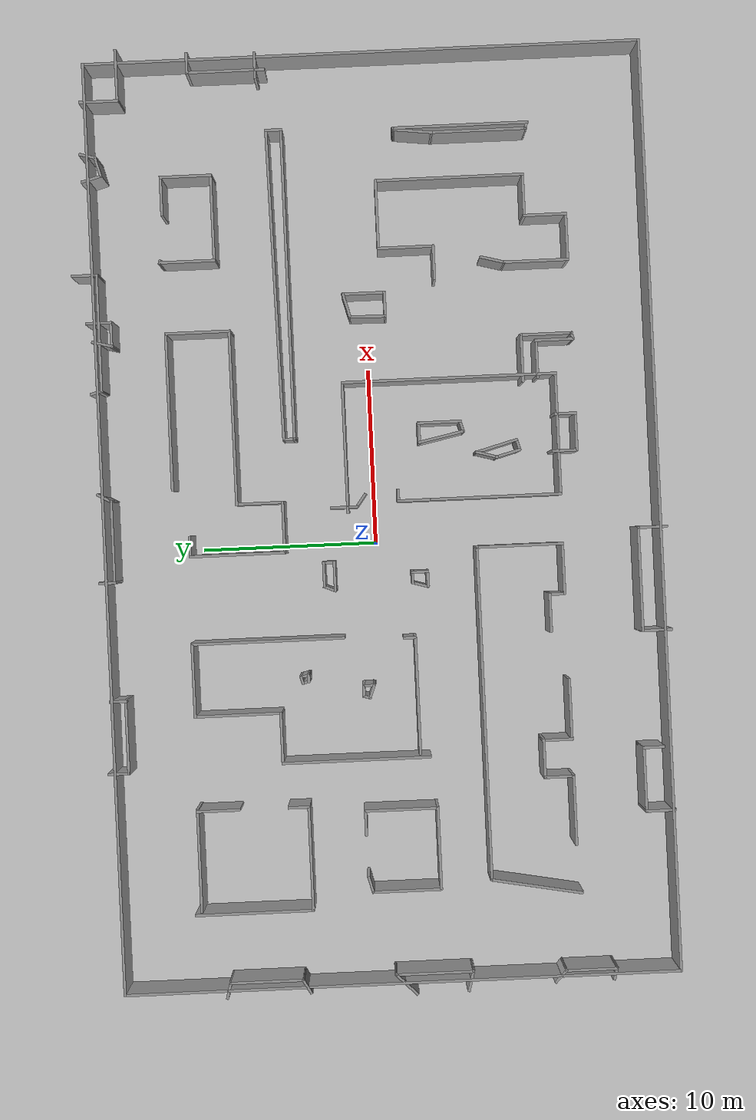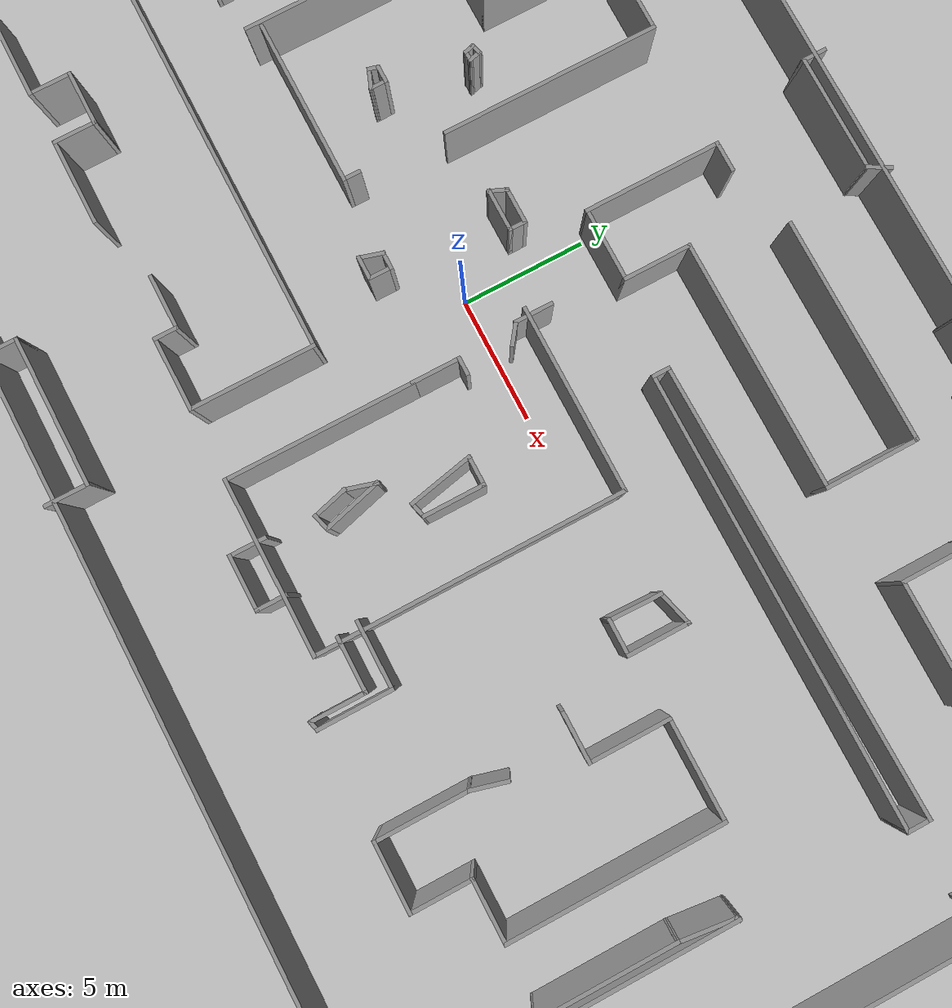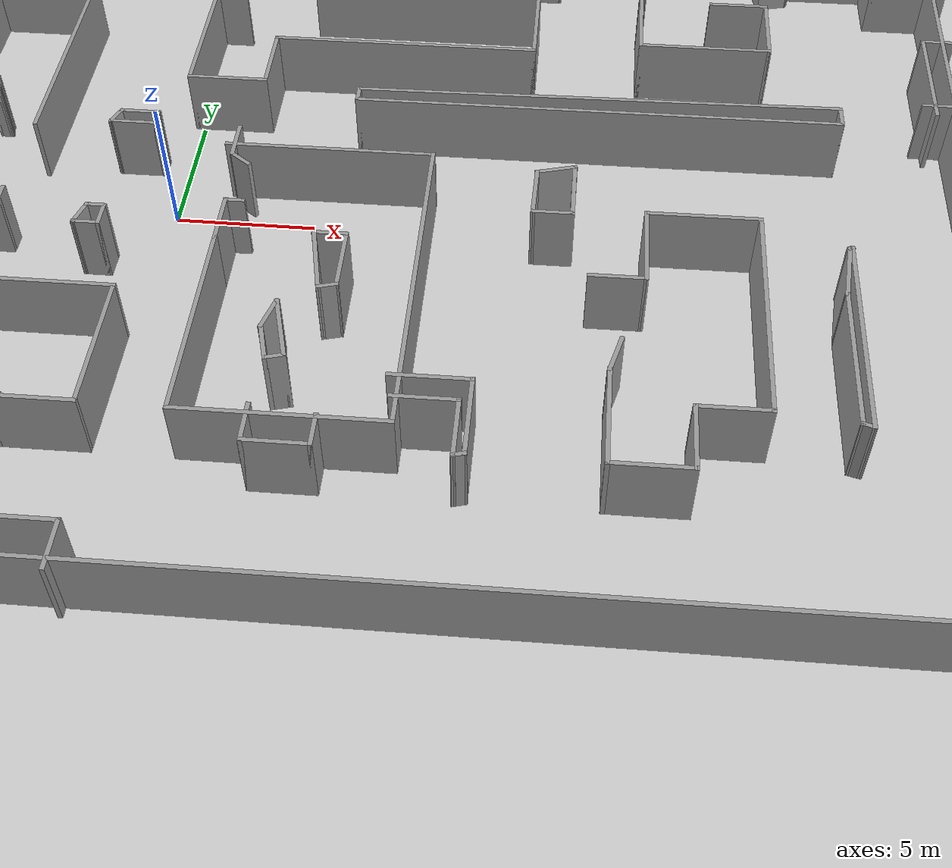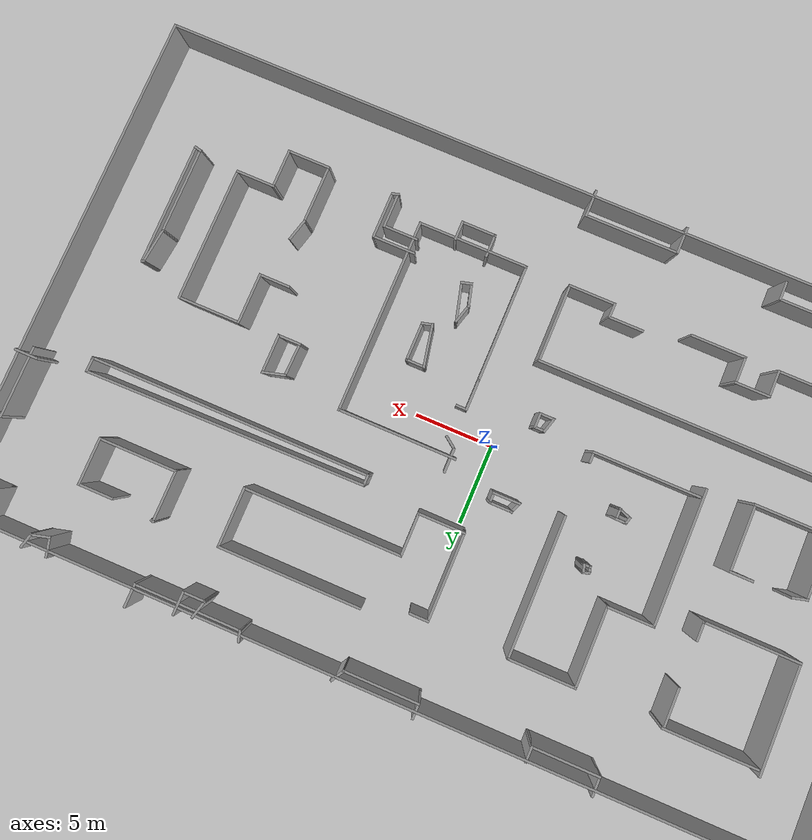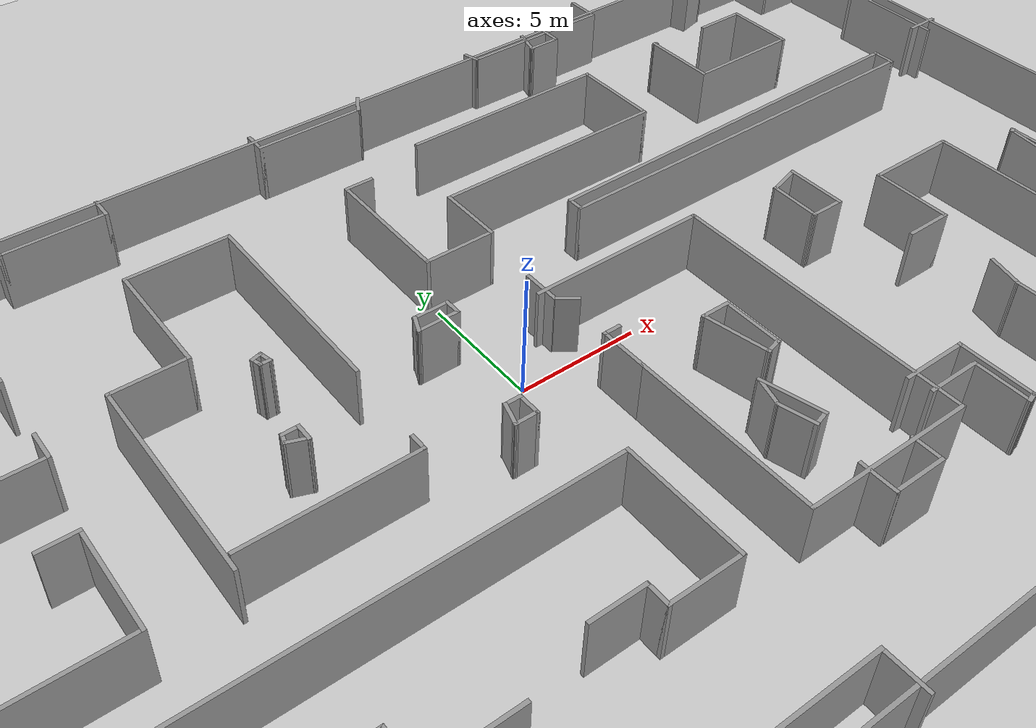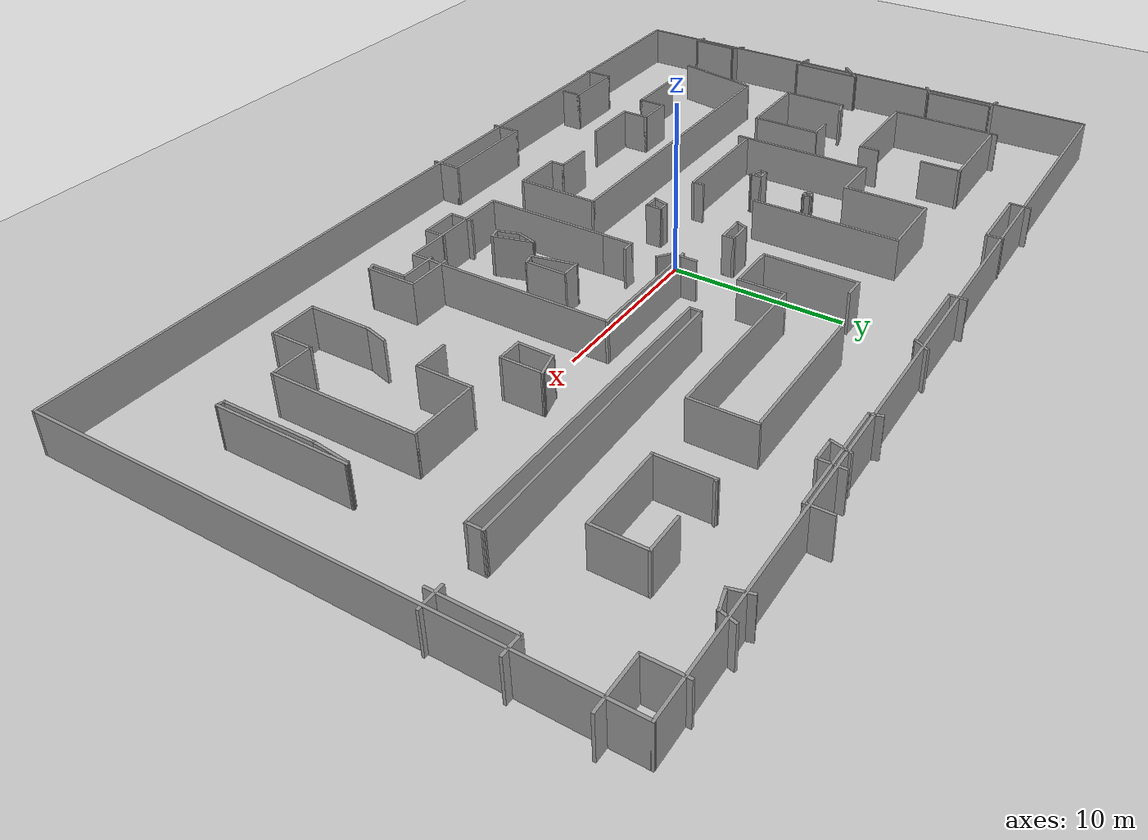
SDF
<sdf version="1.6">
 <world name="default">
  <light name="sun" type="directional">
   <pose>0 0 10 0 -0 0</pose>
   <diffuse>0.8 0.8 0.8 1</diffuse>
   <specular>0.2 0.2 0.2 1</specular>
   <attenuation>
    <range>1000</range>
    <constant>0.9</constant>
    <linear>0.01</linear>
    <quadratic>0.001</quadratic>
   </attenuation>
   <direction>-0.5 0.1 -0.9</direction>
  </light>
  <model name="ground_plane">
   <static>1</static>
   <link name="link">
    <collision name="collision">
     <geometry><plane><normal>0 0 1</normal><size>100 100</size></plane></geometry>
     <surface><friction><ode><mu>100</mu><mu2>50</mu2></ode></friction></surface>
    </collision>
    <visual name="visual">
     <cast_shadows>0</cast_shadows>
     <geometry><plane><normal>0 0 1</normal><size>100 100</size></plane></geometry>
     <material>
      <script><uri>file://media/materials/scripts/gazebo.material</uri><name>Gazebo/Grey</name></script>
     </material>
    </visual>
   </link>
  </model>
  <gravity>0 0 -9.8</gravity>
  <magnetic_field>6e-06 2.3e-05 -4.2e-05</magnetic_field>
  <atmosphere type="adiabatic"/>
  <physics name="default_physics" default="0" type="ode">
   <max_step_size>0.001</max_step_size>
   <real_time_factor>1</real_time_factor>
   <real_time_update_rate>1000</real_time_update_rate>
  </physics>
  <scene><ambient>0.4 0.4 0.4 1</ambient><background>0.7 0.7 0.7 1</background><shadows>1</shadows></scene>
  <audio><device>default</device></audio>
  <spherical_coordinates>
   <surface_model>EARTH_WGS84</surface_model>
   <latitude_deg>0</latitude_deg>
   <longitude_deg>0</longitude_deg>
   <elevation>0</elevation>
   <heading_deg>0</heading_deg>
  </spherical_coordinates>
  <model name="big_bad_building">
   <pose>1.49466 0.02184 0 0 -0 0</pose>
   <link name="Wall_100">
    <collision name="Wall_100_Collision">
     <geometry><box><size>1.75 0.15 2.5</size></box></geometry>
     <pose>0 0 1.25 0 -0 0</pose>
    </collision>
    <visual name="Wall_100_Visual">
     <pose>0 0 1.25 0 -0 0</pose>
     <geometry><box><size>1.75 0.15 2.5</size></box></geometry>
     <material>
      <script><uri>file://media/materials/scripts/gazebo.material</uri><name>Gazebo/Grey</name></script>
      <ambient>1 1 1 1</ambient>
     </material>
     <meta><layer>0</layer></meta>
    </visual>
    <pose>-17.3463 -15.4498 0 0 -0 1.5708</pose>
   </link>
   <link name="Wall_101">
    <collision name="Wall_101_Collision">
     <geometry><box><size>3.75 0.15 2.5</size></box></geometry>
     <pose>0 0 1.25 0 -0 0</pose>
    </collision>
    <visual name="Wall_101_Visual">
     <pose>0 0 1.25 0 -0 0</pose>
     <geometry><box><size>3.75 0.15 2.5</size></box></geometry>
     <material>
      <script><uri>file://media/materials/scripts/gazebo.material</uri><name>Gazebo/Grey</name></script>
      <ambient>1 1 1 1</ambient>
     </material>
     <meta><layer>0</layer></meta>
    </visual>
    <pose>-15.5463 -14.6498 0 0 -0 0</pose>
   </link>
   <link name="Wall_102">
    <collision name="Wall_102_Collision">
     <geometry><box><size>1.25 0.15 2.5</size></box></geometry>
     <pose>0 0 1.25 0 -0 0</pose>
    </collision>
    <visual name="Wall_102_Visual">
     <pose>0 0 1.25 0 -0 0</pose>
     <geometry><box><size>1.25 0.15 2.5</size></box></geometry>
     <material>
      <script><uri>file://media/materials/scripts/gazebo.material</uri><name>Gazebo/Grey</name></script>
      <ambient>1 1 1 1</ambient>
     </material>
     <meta><layer>0</layer></meta>
    </visual>
    <pose>-13.7463 -15.1998 0 0 -0 -1.5708</pose>
   </link>
   <link name="Wall_104">
    <collision name="Wall_104_Collision">
     <geometry><box><size>1.75 0.15 2.5</size></box></geometry>
     <pose>0 0 1.25 0 -0 0</pose>
    </collision>
    <visual name="Wall_104_Visual">
     <pose>0 0 1.25 0 -0 0</pose>
     <geometry><box><size>1.75 0.15 2.5</size></box></geometry>
     <material>
      <script><uri>file://media/materials/scripts/gazebo.material</uri><name>Gazebo/Grey</name></script>
      <ambient>1 1 1 1</ambient>
     </material>
     <meta><layer>0</layer></meta>
    </visual>
    <pose>-7.13039 -15.7037 0 0 -0 1.5708</pose>
   </link>
   <link name="Wall_105">
    <collision name="Wall_105_Collision">
     <geometry><box><size>6 0.15 2.5</size></box></geometry>
     <pose>0 0 1.25 0 -0 0</pose>
    </collision>
    <visual name="Wall_105_Visual">
     <pose>0 0 1.25 0 -0 0</pose>
     <geometry><box><size>6 0.15 2.5</size></box></geometry>
     <material>
      <script><uri>file://media/materials/scripts/gazebo.material</uri><name>Gazebo/Grey</name></script>
      <ambient>1 1 1 1</ambient>
     </material>
     <meta><layer>0</layer></meta>
    </visual>
    <pose>-4.20539 -14.9037 0 0 -0 0</pose>
   </link>
   <link name="Wall_106">
    <collision name="Wall_106_Collision">
     <geometry><box><size>1.75 0.15 2.5</size></box></geometry>
     <pose>0 0 1.25 0 -0 0</pose>
    </collision>
    <visual name="Wall_106_Visual">
     <pose>0 0 1.25 0 -0 0</pose>
     <geometry><box><size>1.75 0.15 2.5</size></box></geometry>
     <material>
      <script><uri>file://media/materials/scripts/gazebo.material</uri><name>Gazebo/Grey</name></script>
      <ambient>1 1 1 1</ambient>
     </material>
     <meta><layer>0</layer></meta>
    </visual>
    <pose>-1.28039 -15.7037 0 0 -0 -1.5708</pose>
   </link>
   <link name="Wall_108">
    <collision name="Wall_108_Collision">
     <geometry><box><size>1.5 0.15 2.5</size></box></geometry>
     <pose>0 0 1.25 0 -0 0</pose>
    </collision>
    <visual name="Wall_108_Visual">
     <pose>0 0 1.25 0 -0 0</pose>
     <geometry><box><size>1.5 0.15 2.5</size></box></geometry>
     <material>
      <script><uri>file://media/materials/scripts/gazebo.material</uri><name>Gazebo/Grey</name></script>
      <ambient>1 1 1 1</ambient>
     </material>
     <meta><layer>0</layer></meta>
    </visual>
    <pose>3.27589 -10.9603 0 0 -0 -1.5708</pose>
   </link>
   <link name="Wall_109">
    <collision name="Wall_109_Collision">
     <geometry><box><size>2.25 0.15 2.5</size></box></geometry>
     <pose>0 0 1.25 0 -0 0</pose>
    </collision>
    <visual name="Wall_109_Visual">
     <pose>0 0 1.25 0 -0 0</pose>
     <geometry><box><size>2.25 0.15 2.5</size></box></geometry>
     <material>
      <script><uri>file://media/materials/scripts/gazebo.material</uri><name>Gazebo/Grey</name></script>
      <ambient>1 1 1 1</ambient>
     </material>
     <meta><layer>0</layer></meta>
    </visual>
    <pose>4.32589 -11.6353 0 0 -0 0</pose>
   </link>
   <link name="Wall_11">
    <collision name="Wall_11_Collision">
     <geometry><box><size>6.75 0.15 2.5</size></box></geometry>
     <pose>0 0 1.25 0 -0 0</pose>
    </collision>
    <visual name="Wall_11_Visual">
     <pose>0 0 1.25 0 -0 0</pose>
     <geometry><box><size>6.75 0.15 2.5</size></box></geometry>
     <material>
      <script><uri>file://media/materials/scripts/gazebo.material</uri><name>Gazebo/Grey</name></script>
      <ambient>1 1 1 1</ambient>
     </material>
     <meta><layer>0</layer></meta>
    </visual>
    <pose>-22.1035 7.75425 0 0 -0 -1.5708</pose>
   </link>
   <link name="Wall_110">
    <collision name="Wall_110_Collision">
     <geometry><box><size>1.25 0.15 2.5</size></box></geometry>
     <pose>0 0 1.25 0 -0 0</pose>
    </collision>
    <visual name="Wall_110_Visual">
     <pose>0 0 1.25 0 -0 0</pose>
     <geometry><box><size>1.25 0.15 2.5</size></box></geometry>
     <material>
      <script><uri>file://media/materials/scripts/gazebo.material</uri><name>Gazebo/Grey</name></script>
      <ambient>1 1 1 1</ambient>
     </material>
     <meta><layer>0</layer></meta>
    </visual>
    <pose>5.37589 -11.0853 0 0 -0 1.5708</pose>
   </link>
   <link name="Wall_112">
    <collision name="Wall_112_Collision">
     <geometry><box><size>2 0.15 2.5</size></box></geometry>
     <pose>0 0 1.25 0 -0 0</pose>
    </collision>
    <visual name="Wall_112_Visual">
     <pose>0 0 1.25 0 -0 0</pose>
     <geometry><box><size>2 0.15 2.5</size></box></geometry>
     <material>
      <script><uri>file://media/materials/scripts/gazebo.material</uri><name>Gazebo/Grey</name></script>
      <ambient>1 1 1 1</ambient>
     </material>
     <meta><layer>0</layer></meta>
    </visual>
    <pose>14.2899 -4.00343 0 0 -0 0</pose>
   </link>
   <link name="Wall_113">
    <collision name="Wall_113_Collision">
     <geometry><box><size>3.25 0.15 2.5</size></box></geometry>
     <pose>0 0 1.25 0 -0 0</pose>
    </collision>
    <visual name="Wall_113_Visual">
     <pose>0 0 1.25 0 -0 0</pose>
     <geometry><box><size>3.25 0.15 2.5</size></box></geometry>
     <material>
      <script><uri>file://media/materials/scripts/gazebo.material</uri><name>Gazebo/Grey</name></script>
      <ambient>1 1 1 1</ambient>
     </material>
     <meta><layer>0</layer></meta>
    </visual>
    <pose>15.2149 -2.45343 0 0 -0 1.5708</pose>
   </link>
   <link name="Wall_114">
    <collision name="Wall_114_Collision">
     <geometry><box><size>4 0.15 2.5</size></box></geometry>
     <pose>0 0 1.25 0 -0 0</pose>
    </collision>
    <visual name="Wall_114_Visual">
     <pose>0 0 1.25 0 -0 0</pose>
     <geometry><box><size>4 0.15 2.5</size></box></geometry>
     <material>
      <script><uri>file://media/materials/scripts/gazebo.material</uri><name>Gazebo/Grey</name></script>
      <ambient>1 1 1 1</ambient>
     </material>
     <meta><layer>0</layer></meta>
    </visual>
    <pose>17.1399 -0.903431 0 0 -0 0</pose>
   </link>
   <link name="Wall_115">
    <collision name="Wall_115_Collision">
     <geometry><box><size>8.5 0.15 2.5</size></box></geometry>
     <pose>0 0 1.25 0 -0 0</pose>
    </collision>
    <visual name="Wall_115_Visual">
     <pose>0 0 1.25 0 -0 0</pose>
     <geometry><box><size>8.5 0.15 2.5</size></box></geometry>
     <material>
      <script><uri>file://media/materials/scripts/gazebo.material</uri><name>Gazebo/Grey</name></script>
      <ambient>1 1 1 1</ambient>
     </material>
     <meta><layer>0</layer></meta>
    </visual>
    <pose>19.0649 -5.07843 0 0 -0 -1.5708</pose>
   </link>
   <link name="Wall_116">
    <collision name="Wall_116_Collision">
     <geometry><box><size>2.5 0.15 2.5</size></box></geometry>
     <pose>0 0 1.25 0 -0 0</pose>
    </collision>
    <visual name="Wall_116_Visual">
     <pose>0 0 1.25 0 -0 0</pose>
     <geometry><box><size>2.5 0.15 2.5</size></box></geometry>
     <material>
      <script><uri>file://media/materials/scripts/gazebo.material</uri><name>Gazebo/Grey</name></script>
      <ambient>1 1 1 1</ambient>
     </material>
     <meta><layer>0</layer></meta>
    </visual>
    <pose>17.8899 -9.25343 0 0 -0 3.14159</pose>
   </link>
   <link name="Wall_117">
    <collision name="Wall_117_Collision">
     <geometry><box><size>2.5 0.15 2.5</size></box></geometry>
     <pose>0 0 1.25 0 -0 0</pose>
    </collision>
    <visual name="Wall_117_Visual">
     <pose>0 0 1.25 0 -0 0</pose>
     <geometry><box><size>2.5 0.15 2.5</size></box></geometry>
     <material>
      <script><uri>file://media/materials/scripts/gazebo.material</uri><name>Gazebo/Grey</name></script>
      <ambient>1 1 1 1</ambient>
     </material>
     <meta><layer>0</layer></meta>
    </visual>
    <pose>16.7149 -10.4284 0 0 -0 -1.5708</pose>
   </link>
   <link name="Wall_118">
    <collision name="Wall_118_Collision">
     <geometry><box><size>2.75 0.15 2.5</size></box></geometry>
     <pose>0 0 1.25 0 -0 0</pose>
    </collision>
    <visual name="Wall_118_Visual">
     <pose>0 0 1.25 0 -0 0</pose>
     <geometry><box><size>2.75 0.15 2.5</size></box></geometry>
     <material>
      <script><uri>file://media/materials/scripts/gazebo.material</uri><name>Gazebo/Grey</name></script>
      <ambient>1 1 1 1</ambient>
     </material>
     <meta><layer>0</layer></meta>
    </visual>
    <pose>15.4149 -11.6034 0 0 -0 3.14159</pose>
   </link>
   <link name="Wall_119">
    <collision name="Wall_119_Collision">
     <geometry><box><size>3.75 0.15 2.5</size></box></geometry>
     <pose>0 0 1.25 0 -0 0</pose>
    </collision>
    <visual name="Wall_119_Visual">
     <pose>0 0 1.25 0 -0 0</pose>
     <geometry><box><size>3.75 0.15 2.5</size></box></geometry>
     <material>
      <script><uri>file://media/materials/scripts/gazebo.material</uri><name>Gazebo/Grey</name></script>
      <ambient>1 1 1 1</ambient>
     </material>
     <meta><layer>0</layer></meta>
    </visual>
    <pose>14.1149 -9.80343 0 0 -0 1.5708</pose>
   </link>
   <link name="Wall_12">
    <collision name="Wall_12_Collision">
     <geometry><box><size>6 0.15 2.5</size></box></geometry>
     <pose>0 0 1.25 0 -0 0</pose>
    </collision>
    <visual name="Wall_12_Visual">
     <pose>0 0 1.25 0 -0 0</pose>
     <geometry><box><size>6 0.15 2.5</size></box></geometry>
     <material>
      <script><uri>file://media/materials/scripts/gazebo.material</uri><name>Gazebo/Grey</name></script>
      <ambient>1 1 1 1</ambient>
     </material>
     <meta><layer>0</layer></meta>
    </visual>
    <pose>-19.1785 4.45425 0 0 -0 0</pose>
   </link>
   <link name="Wall_120">
    <collision name="Wall_120_Collision">
     <geometry><box><size>1.5 0.15 2.5</size></box></geometry>
     <pose>0 0 1.25 0 -0 0</pose>
    </collision>
    <visual name="Wall_120_Visual">
     <pose>0 0 1.25 0 -0 0</pose>
     <geometry><box><size>1.5 0.15 2.5</size></box></geometry>
     <material>
      <script><uri>file://media/materials/scripts/gazebo.material</uri><name>Gazebo/Grey</name></script>
      <ambient>1 1 1 1</ambient>
     </material>
     <meta><layer>0</layer></meta>
    </visual>
    <pose>14.2896 -7.35143 0 0 -0 1.309</pose>
   </link>
   <link name="Wall_122">
    <collision name="Wall_122_Collision">
     <geometry><box><size>1.5 0.15 2.5</size></box></geometry>
     <pose>0 0 1.25 0 -0 0</pose>
    </collision>
    <visual name="Wall_122_Visual">
     <pose>0 0 1.25 0 -0 0</pose>
     <geometry><box><size>1.5 0.15 2.5</size></box></geometry>
     <material>
      <script><uri>file://media/materials/scripts/gazebo.material</uri><name>Gazebo/Grey</name></script>
      <ambient>1 1 1 1</ambient>
     </material>
     <meta><layer>0</layer></meta>
    </visual>
    <pose>12.0499 1.05715 0 0 -0 0.261799</pose>
   </link>
   <link name="Wall_123">
    <collision name="Wall_123_Collision">
     <geometry><box><size>2.5 0.15 2.5</size></box></geometry>
     <pose>0 0 1.25 0 -0 0</pose>
    </collision>
    <visual name="Wall_123_Visual">
     <pose>0 0 1.25 0 -0 0</pose>
     <geometry><box><size>2.5 0.15 2.5</size></box></geometry>
     <material>
      <script><uri>file://media/materials/scripts/gazebo.material</uri><name>Gazebo/Grey</name></script>
      <ambient>1 1 1 1</ambient>
     </material>
     <meta><layer>0</layer></meta>
    </visual>
    <pose>12.7019 0.056852 0 0 -0 -1.5708</pose>
   </link>
   <link name="Wall_124">
    <collision name="Wall_124_Collision">
     <geometry><box><size>1.5 0.15 2.5</size></box></geometry>
     <pose>0 0 1.25 0 -0 0</pose>
    </collision>
    <visual name="Wall_124_Visual">
     <pose>0 0 1.25 0 -0 0</pose>
     <geometry><box><size>1.5 0.15 2.5</size></box></geometry>
     <material>
      <script><uri>file://media/materials/scripts/gazebo.material</uri><name>Gazebo/Grey</name></script>
      <ambient>1 1 1 1</ambient>
     </material>
     <meta><layer>0</layer></meta>
    </visual>
    <pose>12.0269 -1.11815 0 0 -0 3.14159</pose>
   </link>
   <link name="Wall_125">
    <collision name="Wall_125_Collision">
     <geometry><box><size>2.15112 0.15 2.5</size></box></geometry>
     <pose>0 0 1.25 0 -0 0</pose>
    </collision>
    <visual name="Wall_125_Visual">
     <pose>0 0 1.25 0 -0 0</pose>
     <geometry><box><size>2.15112 0.15 2.5</size></box></geometry>
     <material>
      <script><uri>file://media/materials/scripts/gazebo.material</uri><name>Gazebo/Grey</name></script>
      <ambient>1 1 1 1</ambient>
     </material>
     <meta><layer>0</layer></meta>
    </visual>
    <pose>11.3749 -0.117851 0 0 -0 1.54781</pose>
   </link>
   <link name="Wall_127">
    <collision name="Wall_127_Collision">
     <geometry><box><size>5.5 0.15 2.5</size></box></geometry>
     <pose>0 0 1.25 0 -0 0</pose>
    </collision>
    <visual name="Wall_127_Visual">
     <pose>0 0 1.25 0 -0 0</pose>
     <geometry><box><size>5.5 0.15 2.5</size></box></geometry>
     <material>
      <script><uri>file://media/materials/scripts/gazebo.material</uri><name>Gazebo/Grey</name></script>
      <ambient>1 1 1 1</ambient>
     </material>
     <meta><layer>0</layer></meta>
    </visual>
    <pose>21.6773 -6.86879 0 0 -0 -1.5708</pose>
   </link>
   <link name="Wall_128">
    <collision name="Wall_128_Collision">
     <geometry><box><size>0.5 0.15 2.5</size></box></geometry>
     <pose>0 0 1.25 0 -0 0</pose>
    </collision>
    <visual name="Wall_128_Visual">
     <pose>0 0 1.25 0 -0 0</pose>
     <geometry><box><size>0.5 0.15 2.5</size></box></geometry>
     <material>
      <script><uri>file://media/materials/scripts/gazebo.material</uri><name>Gazebo/Grey</name></script>
      <ambient>1 1 1 1</ambient>
     </material>
     <meta><layer>0</layer></meta>
    </visual>
    <pose>21.8463 -9.58908 0 0 -0 -0.261799</pose>
   </link>
   <link name="Wall_129">
    <collision name="Wall_129_Collision">
     <geometry><box><size>7.75 0.15 2.5</size></box></geometry>
     <pose>0 0 1.25 0 -0 0</pose>
    </collision>
    <visual name="Wall_129_Visual">
     <pose>0 0 1.25 0 -0 0</pose>
     <geometry><box><size>7.75 0.15 2.5</size></box></geometry>
     <material>
      <script><uri>file://media/materials/scripts/gazebo.material</uri><name>Gazebo/Grey</name></script>
      <ambient>1 1 1 1</ambient>
     </material>
     <meta><layer>0</layer></meta>
    </visual>
    <pose>22.0153 -5.83438 0 0 -0 1.5708</pose>
   </link>
   <link name="Wall_13">
    <collision name="Wall_13_Collision">
     <geometry><box><size>1.25 0.15 2.5</size></box></geometry>
     <pose>0 0 1.25 0 -0 0</pose>
    </collision>
    <visual name="Wall_13_Visual">
     <pose>0 0 1.25 0 -0 0</pose>
     <geometry><box><size>1.25 0.15 2.5</size></box></geometry>
     <material>
      <script><uri>file://media/materials/scripts/gazebo.material</uri><name>Gazebo/Grey</name></script>
      <ambient>1 1 1 1</ambient>
     </material>
     <meta><layer>0</layer></meta>
    </visual>
    <pose>-16.2535 5.00425 0 0 -0 1.5708</pose>
   </link>
   <link name="Wall_130">
    <collision name="Wall_130_Collision">
     <geometry><box><size>0.25 0.15 2.5</size></box></geometry>
     <pose>0 0 1.25 0 -0 0</pose>
    </collision>
    <visual name="Wall_130_Visual">
     <pose>0 0 1.25 0 -0 0</pose>
     <geometry><box><size>0.25 0.15 2.5</size></box></geometry>
     <material>
      <script><uri>file://media/materials/scripts/gazebo.material</uri><name>Gazebo/Grey</name></script>
      <ambient>1 1 1 1</ambient>
     </material>
     <meta><layer>0</layer></meta>
    </visual>
    <pose>21.972 -2.05938 0 0 -0 -2.61799</pose>
   </link>
   <link name="Wall_131">
    <collision name="Wall_131_Collision">
     <geometry><box><size>2.27435 0.15 2.5</size></box></geometry>
     <pose>0 0 1.25 0 -0 0</pose>
    </collision>
    <visual name="Wall_131_Visual">
     <pose>0 0 1.25 0 -0 0</pose>
     <geometry><box><size>2.27435 0.15 2.5</size></box></geometry>
     <material>
      <script><uri>file://media/materials/scripts/gazebo.material</uri><name>Gazebo/Grey</name></script>
      <ambient>1 1 1 1</ambient>
     </material>
     <meta><layer>0</layer></meta>
    </visual>
    <pose>21.803 -3.13908 0 0 -0 -1.68945</pose>
   </link>
   <link name="Wall_133">
    <collision name="Wall_133_Collision">
     <geometry><box><size>2.75 0.15 2.5</size></box></geometry>
     <pose>0 0 1.25 0 -0 0</pose>
    </collision>
    <visual name="Wall_133_Visual">
     <pose>0 0 1.25 0 -0 0</pose>
     <geometry><box><size>2.75 0.15 2.5</size></box></geometry>
     <material>
      <script><uri>file://media/materials/scripts/gazebo.material</uri><name>Gazebo/Grey</name></script>
      <ambient>1 1 1 1</ambient>
     </material>
     <meta><layer>0</layer></meta>
    </visual>
    <pose>8.63688 -8.7624 0 0 -0 0</pose>
   </link>
   <link name="Wall_134">
    <collision name="Wall_134_Collision">
     <geometry><box><size>3 0.15 2.5</size></box></geometry>
     <pose>0 0 1.25 0 -0 0</pose>
    </collision>
    <visual name="Wall_134_Visual">
     <pose>0 0 1.25 0 -0 0</pose>
     <geometry><box><size>3 0.15 2.5</size></box></geometry>
     <material>
      <script><uri>file://media/materials/scripts/gazebo.material</uri><name>Gazebo/Grey</name></script>
      <ambient>1 1 1 1</ambient>
     </material>
     <meta><layer>0</layer></meta>
    </visual>
    <pose>9.93688 -10.1874 0 0 -0 -1.5708</pose>
   </link>
   <link name="Wall_135">
    <collision name="Wall_135_Collision">
     <geometry><box><size>0.5 0.15 2.5</size></box></geometry>
     <pose>0 0 1.25 0 -0 0</pose>
    </collision>
    <visual name="Wall_135_Visual">
     <pose>0 0 1.25 0 -0 0</pose>
     <geometry><box><size>0.5 0.15 2.5</size></box></geometry>
     <material>
      <script><uri>file://media/materials/scripts/gazebo.material</uri><name>Gazebo/Grey</name></script>
      <ambient>1 1 1 1</ambient>
     </material>
     <meta><layer>0</layer></meta>
    </visual>
    <pose>9.76784 -11.6577 0 0 -0 -2.87979</pose>
   </link>
   <link name="Wall_136">
    <collision name="Wall_136_Collision">
     <geometry><box><size>2.25 0.15 2.5</size></box></geometry>
     <pose>0 0 1.25 0 -0 0</pose>
    </collision>
    <visual name="Wall_136_Visual">
     <pose>0 0 1.25 0 -0 0</pose>
     <geometry><box><size>2.25 0.15 2.5</size></box></geometry>
     <material>
      <script><uri>file://media/materials/scripts/gazebo.material</uri><name>Gazebo/Grey</name></script>
      <ambient>1 1 1 1</ambient>
     </material>
     <meta><layer>0</layer></meta>
    </visual>
    <pose>9.59881 -10.653 0 0 -0 1.5708</pose>
   </link>
   <link name="Wall_137">
    <collision name="Wall_137_Collision">
     <geometry><box><size>2.25 0.15 2.5</size></box></geometry>
     <pose>0 0 1.25 0 -0 0</pose>
    </collision>
    <visual name="Wall_137_Visual">
     <pose>0 0 1.25 0 -0 0</pose>
     <geometry><box><size>2.25 0.15 2.5</size></box></geometry>
     <material>
      <script><uri>file://media/materials/scripts/gazebo.material</uri><name>Gazebo/Grey</name></script>
      <ambient>1 1 1 1</ambient>
     </material>
     <meta><layer>0</layer></meta>
    </visual>
    <pose>8.54881 -9.60299 0 0 -0 3.14159</pose>
   </link>
   <link name="Wall_139">
    <collision name="Wall_139_Collision">
     <geometry><box><size>1.75 0.15 2.5</size></box></geometry>
     <pose>0 0 1.25 0 -0 0</pose>
    </collision>
    <visual name="Wall_139_Visual">
     <pose>0 0 1.25 0 -0 0</pose>
     <geometry><box><size>1.75 0.15 2.5</size></box></geometry>
     <material>
      <script><uri>file://media/materials/scripts/gazebo.material</uri><name>Gazebo/Grey</name></script>
      <ambient>1 1 1 1</ambient>
     </material>
     <meta><layer>0</layer></meta>
    </visual>
    <pose>-3.28465 2.40532 0 0 -0 0</pose>
   </link>
   <link name="Wall_140">
    <collision name="Wall_140_Collision">
     <geometry><box><size>0.75 0.15 2.5</size></box></geometry>
     <pose>0 0 1.25 0 -0 0</pose>
    </collision>
    <visual name="Wall_140_Visual">
     <pose>0 0 1.25 0 -0 0</pose>
     <geometry><box><size>0.75 0.15 2.5</size></box></geometry>
     <material>
      <script><uri>file://media/materials/scripts/gazebo.material</uri><name>Gazebo/Grey</name></script>
      <ambient>1 1 1 1</ambient>
     </material>
     <meta><layer>0</layer></meta>
    </visual>
    <pose>-2.48465 2.70532 0 0 -0 1.5708</pose>
   </link>
   <link name="Wall_141">
    <collision name="Wall_141_Collision">
     <geometry><box><size>1.5 0.15 2.5</size></box></geometry>
     <pose>0 0 1.25 0 -0 0</pose>
    </collision>
    <visual name="Wall_141_Visual">
     <pose>0 0 1.25 0 -0 0</pose>
     <geometry><box><size>1.5 0.15 2.5</size></box></geometry>
     <material>
      <script><uri>file://media/materials/scripts/gazebo.material</uri><name>Gazebo/Grey</name></script>
      <ambient>1 1 1 1</ambient>
     </material>
     <meta><layer>0</layer></meta>
    </visual>
    <pose>-3.15965 3.00532 0 0 -0 3.14159</pose>
   </link>
   <link name="Wall_142">
    <collision name="Wall_142_Collision">
     <geometry><box><size>0.8 0.15 2.5</size></box></geometry>
     <pose>0 0 1.25 0 -0 0</pose>
    </collision>
    <visual name="Wall_142_Visual">
     <pose>0 0 1.25 0 -0 0</pose>
     <geometry><box><size>0.8 0.15 2.5</size></box></geometry>
     <material>
      <script><uri>file://media/materials/scripts/gazebo.material</uri><name>Gazebo/Grey</name></script>
      <ambient>1 1 1 1</ambient>
     </material>
     <meta><layer>0</layer></meta>
    </visual>
    <pose>-3.95965 2.70532 0 0 -0 -1.96559</pose>
   </link>
   <link name="Wall_144">
    <collision name="Wall_144_Collision">
     <geometry><box><size>1.25 0.15 2.5</size></box></geometry>
     <pose>0 0 1.25 0 -0 0</pose>
    </collision>
    <visual name="Wall_144_Visual">
     <pose>0 0 1.25 0 -0 0</pose>
     <geometry><box><size>1.25 0.15 2.5</size></box></geometry>
     <material>
      <script><uri>file://media/materials/scripts/gazebo.material</uri><name>Gazebo/Grey</name></script>
      <ambient>1 1 1 1</ambient>
     </material>
     <meta><layer>0</layer></meta>
    </visual>
    <pose>-13.913 15.0993 0 0 -0 -1.5708</pose>
   </link>
   <link name="Wall_145">
    <collision name="Wall_145_Collision">
     <geometry><box><size>4.25 0.15 2.5</size></box></geometry>
     <pose>0 0 1.25 0 -0 0</pose>
    </collision>
    <visual name="Wall_145_Visual">
     <pose>0 0 1.25 0 -0 0</pose>
     <geometry><box><size>4.25 0.15 2.5</size></box></geometry>
     <material>
      <script><uri>file://media/materials/scripts/gazebo.material</uri><name>Gazebo/Grey</name></script>
      <ambient>1 1 1 1</ambient>
     </material>
     <meta><layer>0</layer></meta>
    </visual>
    <pose>-11.863 14.5493 0 0 -0 0</pose>
   </link>
   <link name="Wall_146">
    <collision name="Wall_146_Collision">
     <geometry><box><size>1 0.15 2.5</size></box></geometry>
     <pose>0 0 1.25 0 -0 0</pose>
    </collision>
    <visual name="Wall_146_Visual">
     <pose>0 0 1.25 0 -0 0</pose>
     <geometry><box><size>1 0.15 2.5</size></box></geometry>
     <material>
      <script><uri>file://media/materials/scripts/gazebo.material</uri><name>Gazebo/Grey</name></script>
      <ambient>1 1 1 1</ambient>
     </material>
     <meta><layer>0</layer></meta>
    </visual>
    <pose>-9.81303 14.9743 0 0 -0 1.5708</pose>
   </link>
   <link name="Wall_148">
    <collision name="Wall_148_Collision">
     <geometry><box><size>1 0.15 2.5</size></box></geometry>
     <pose>0 0 1.25 0 -0 0</pose>
    </collision>
    <visual name="Wall_148_Visual">
     <pose>0 0 1.25 0 -0 0</pose>
     <geometry><box><size>1 0.15 2.5</size></box></geometry>
     <material>
      <script><uri>file://media/materials/scripts/gazebo.material</uri><name>Gazebo/Grey</name></script>
      <ambient>1 1 1 1</ambient>
     </material>
     <meta><layer>0</layer></meta>
    </visual>
    <pose>-3.0878 15.3082 0 0 -0 -1.5708</pose>
   </link>
   <link name="Wall_149">
    <collision name="Wall_149_Collision">
     <geometry><box><size>4.75 0.15 2.5</size></box></geometry>
     <pose>0 0 1.25 0 -0 0</pose>
    </collision>
    <visual name="Wall_149_Visual">
     <pose>0 0 1.25 0 -0 0</pose>
     <geometry><box><size>4.75 0.15 2.5</size></box></geometry>
     <material>
      <script><uri>file://media/materials/scripts/gazebo.material</uri><name>Gazebo/Grey</name></script>
      <ambient>1 1 1 1</ambient>
     </material>
     <meta><layer>0</layer></meta>
    </visual>
    <pose>-0.787797 14.8832 0 0 -0 0</pose>
   </link>
   <link name="Wall_15">
    <collision name="Wall_15_Collision">
     <geometry><box><size>1.5 0.15 2.5</size></box></geometry>
     <pose>0 0 1.25 0 -0 0</pose>
    </collision>
    <visual name="Wall_15_Visual">
     <pose>0 0 1.25 0 -0 0</pose>
     <geometry><box><size>1.5 0.15 2.5</size></box></geometry>
     <material>
      <script><uri>file://media/materials/scripts/gazebo.material</uri><name>Gazebo/Grey</name></script>
      <ambient>1 1 1 1</ambient>
     </material>
     <meta><layer>0</layer></meta>
    </visual>
    <pose>-17.3058 1.26316 0 0 -0 0</pose>
   </link>
   <link name="Wall_150">
    <collision name="Wall_150_Collision">
     <geometry><box><size>1 0.15 2.5</size></box></geometry>
     <pose>0 0 1.25 0 -0 0</pose>
    </collision>
    <visual name="Wall_150_Visual">
     <pose>0 0 1.25 0 -0 0</pose>
     <geometry><box><size>1 0.15 2.5</size></box></geometry>
     <material>
      <script><uri>file://media/materials/scripts/gazebo.material</uri><name>Gazebo/Grey</name></script>
      <ambient>1 1 1 1</ambient>
     </material>
     <meta><layer>0</layer></meta>
    </visual>
    <pose>1.7247 15.2513 0 0 -0 1.0472</pose>
   </link>
   <link name="Wall_152">
    <collision name="Wall_152_Collision">
     <geometry><box><size>0.75 0.15 2.5</size></box></geometry>
     <pose>0 0 1.25 0 -0 0</pose>
    </collision>
    <visual name="Wall_152_Visual">
     <pose>0 0 1.25 0 -0 0</pose>
     <geometry><box><size>0.75 0.15 2.5</size></box></geometry>
     <material>
      <script><uri>file://media/materials/scripts/gazebo.material</uri><name>Gazebo/Grey</name></script>
      <ambient>1 1 1 1</ambient>
     </material>
     <meta><layer>0</layer></meta>
    </visual>
    <pose>7.73116 15.4434 0 0 -0 -1.309</pose>
   </link>
   <link name="Wall_153">
    <collision name="Wall_153_Collision">
     <geometry><box><size>6.75 0.15 2.5</size></box></geometry>
     <pose>0 0 1.25 0 -0 0</pose>
    </collision>
    <visual name="Wall_153_Visual">
     <pose>0 0 1.25 0 -0 0</pose>
     <geometry><box><size>6.75 0.15 2.5</size></box></geometry>
     <material>
      <script><uri>file://media/materials/scripts/gazebo.material</uri><name>Gazebo/Grey</name></script>
      <ambient>1 1 1 1</ambient>
     </material>
     <meta><layer>0</layer></meta>
    </visual>
    <pose>11.1088 15.1537 0 0 -0 0</pose>
   </link>
   <link name="Wall_154">
    <collision name="Wall_154_Collision">
     <geometry><box><size>1.5 0.15 2.5</size></box></geometry>
     <pose>0 0 1.25 0 -0 0</pose>
    </collision>
    <visual name="Wall_154_Visual">
     <pose>0 0 1.25 0 -0 0</pose>
     <geometry><box><size>1.5 0.15 2.5</size></box></geometry>
     <material>
      <script><uri>file://media/materials/scripts/gazebo.material</uri><name>Gazebo/Grey</name></script>
      <ambient>1 1 1 1</ambient>
     </material>
     <meta><layer>0</layer></meta>
    </visual>
    <pose>14.4088 15.8287 0 0 -0 1.5708</pose>
   </link>
   <link name="Wall_156">
    <collision name="Wall_156_Collision">
     <geometry><box><size>1.5 0.15 2.5</size></box></geometry>
     <pose>0 0 1.25 0 -0 0</pose>
    </collision>
    <visual name="Wall_156_Visual">
     <pose>0 0 1.25 0 -0 0</pose>
     <geometry><box><size>1.5 0.15 2.5</size></box></geometry>
     <material>
      <script><uri>file://media/materials/scripts/gazebo.material</uri><name>Gazebo/Grey</name></script>
      <ambient>1 1 1 1</ambient>
     </material>
     <meta><layer>0</layer></meta>
    </visual>
    <pose>11.6815 15.1421 0 0 -0 -1.5708</pose>
   </link>
   <link name="Wall_157">
    <collision name="Wall_157_Collision">
     <geometry><box><size>1.5 0.15 2.5</size></box></geometry>
     <pose>0 0 1.25 0 -0 0</pose>
    </collision>
    <visual name="Wall_157_Visual">
     <pose>0 0 1.25 0 -0 0</pose>
     <geometry><box><size>1.5 0.15 2.5</size></box></geometry>
     <material>
      <script><uri>file://media/materials/scripts/gazebo.material</uri><name>Gazebo/Grey</name></script>
      <ambient>1 1 1 1</ambient>
     </material>
     <meta><layer>0</layer></meta>
    </visual>
    <pose>11.0065 14.4671 0 0 -0 3.14159</pose>
   </link>
   <link name="Wall_158">
    <collision name="Wall_158_Collision">
     <geometry><box><size>1.25 0.15 2.5</size></box></geometry>
     <pose>0 0 1.25 0 -0 0</pose>
    </collision>
    <visual name="Wall_158_Visual">
     <pose>0 0 1.25 0 -0 0</pose>
     <geometry><box><size>1.25 0.15 2.5</size></box></geometry>
     <material>
      <script><uri>file://media/materials/scripts/gazebo.material</uri><name>Gazebo/Grey</name></script>
      <ambient>1 1 1 1</ambient>
     </material>
     <meta><layer>0</layer></meta>
    </visual>
    <pose>10.4739 14.9984 0 0 -0 1.309</pose>
   </link>
   <link name="Wall_16">
    <collision name="Wall_16_Collision">
     <geometry><box><size>4.25 0.15 2.5</size></box></geometry>
     <pose>0 0 1.25 0 -0 0</pose>
    </collision>
    <visual name="Wall_16_Visual">
     <pose>0 0 1.25 0 -0 0</pose>
     <geometry><box><size>4.25 0.15 2.5</size></box></geometry>
     <material>
      <script><uri>file://media/materials/scripts/gazebo.material</uri><name>Gazebo/Grey</name></script>
      <ambient>1 1 1 1</ambient>
     </material>
     <meta><layer>0</layer></meta>
    </visual>
    <pose>-16.6308 -0.786836 0 0 -0 -1.5708</pose>
   </link>
   <link name="Wall_160">
    <collision name="Wall_160_Collision">
     <geometry><box><size>2.25 0.15 2.5</size></box></geometry>
     <pose>0 0 1.25 0 -0 0</pose>
    </collision>
    <visual name="Wall_160_Visual">
     <pose>0 0 1.25 0 -0 0</pose>
     <geometry><box><size>2.25 0.15 2.5</size></box></geometry>
     <material>
      <script><uri>file://media/materials/scripts/gazebo.material</uri><name>Gazebo/Grey</name></script>
      <ambient>1 1 1 1</ambient>
     </material>
     <meta><layer>0</layer></meta>
    </visual>
    <pose>24.269 14.5993 0 0 -0 -1.5708</pose>
   </link>
   <link name="Wall_161">
    <collision name="Wall_161_Collision">
     <geometry><box><size>3 0.15 2.5</size></box></geometry>
     <pose>0 0 1.25 0 -0 0</pose>
    </collision>
    <visual name="Wall_161_Visual">
     <pose>0 0 1.25 0 -0 0</pose>
     <geometry><box><size>3 0.15 2.5</size></box></geometry>
     <material>
      <script><uri>file://media/materials/scripts/gazebo.material</uri><name>Gazebo/Grey</name></script>
      <ambient>1 1 1 1</ambient>
     </material>
     <meta><layer>0</layer></meta>
    </visual>
    <pose>25.694 13.5493 0 0 -0 0</pose>
   </link>
   <link name="Wall_163">
    <collision name="Wall_163_Collision">
     <geometry><box><size>1.25 0.15 2.5</size></box></geometry>
     <pose>0 0 1.25 0 -0 0</pose>
    </collision>
    <visual name="Wall_163_Visual">
     <pose>0 0 1.25 0 -0 0</pose>
     <geometry><box><size>1.25 0.15 2.5</size></box></geometry>
     <material>
      <script><uri>file://media/materials/scripts/gazebo.material</uri><name>Gazebo/Grey</name></script>
      <ambient>1 1 1 1</ambient>
     </material>
     <meta><layer>0</layer></meta>
    </visual>
    <pose>19.8798 15.202 0 0 -0 -1.309</pose>
   </link>
   <link name="Wall_164">
    <collision name="Wall_164_Collision">
     <geometry><box><size>1.25 0.15 2.5</size></box></geometry>
     <pose>0 0 1.25 0 -0 0</pose>
    </collision>
    <visual name="Wall_164_Visual">
     <pose>0 0 1.25 0 -0 0</pose>
     <geometry><box><size>1.25 0.15 2.5</size></box></geometry>
     <material>
      <script><uri>file://media/materials/scripts/gazebo.material</uri><name>Gazebo/Grey</name></script>
      <ambient>1 1 1 1</ambient>
     </material>
     <meta><layer>0</layer></meta>
    </visual>
    <pose>20.5535 14.813 0 0 -0 0.261799</pose>
   </link>
   <link name="Wall_165">
    <collision name="Wall_165_Collision">
     <geometry><box><size>1 0.15 2.5</size></box></geometry>
     <pose>0 0 1.25 0 -0 0</pose>
    </collision>
    <visual name="Wall_165_Visual">
     <pose>0 0 1.25 0 -0 0</pose>
     <geometry><box><size>1 0.15 2.5</size></box></geometry>
     <material>
      <script><uri>file://media/materials/scripts/gazebo.material</uri><name>Gazebo/Grey</name></script>
      <ambient>1 1 1 1</ambient>
     </material>
     <meta><layer>0</layer></meta>
    </visual>
    <pose>21.1947 15.3659 0 0 -0 1.309</pose>
   </link>
   <link name="Wall_167">
    <collision name="Wall_167_Collision">
     <geometry><box><size>1.25 0.15 2.5</size></box></geometry>
     <pose>0 0 1.25 0 -0 0</pose>
    </collision>
    <visual name="Wall_167_Visual">
     <pose>0 0 1.25 0 -0 0</pose>
     <geometry><box><size>1.25 0.15 2.5</size></box></geometry>
     <material>
      <script><uri>file://media/materials/scripts/gazebo.material</uri><name>Gazebo/Grey</name></script>
      <ambient>1 1 1 1</ambient>
     </material>
     <meta><layer>0</layer></meta>
    </visual>
    <pose>26.2365 9.52339 0 0 -0 3.14159</pose>
   </link>
   <link name="Wall_168">
    <collision name="Wall_168_Collision">
     <geometry><box><size>4.5 0.15 2.5</size></box></geometry>
     <pose>0 0 1.25 0 -0 0</pose>
    </collision>
    <visual name="Wall_168_Visual">
     <pose>0 0 1.25 0 -0 0</pose>
     <geometry><box><size>4.5 0.15 2.5</size></box></geometry>
     <material>
      <script><uri>file://media/materials/scripts/gazebo.material</uri><name>Gazebo/Grey</name></script>
      <ambient>1 1 1 1</ambient>
     </material>
     <meta><layer>0</layer></meta>
    </visual>
    <pose>25.6865 7.34839 0 0 -0 -1.5708</pose>
   </link>
   <link name="Wall_17">
    <collision name="Wall_17_Collision">
     <geometry><box><size>4.75 0.15 2.5</size></box></geometry>
     <pose>0 0 1.25 0 -0 0</pose>
    </collision>
    <visual name="Wall_17_Visual">
     <pose>0 0 1.25 0 -0 0</pose>
     <geometry><box><size>4.75 0.15 2.5</size></box></geometry>
     <material>
      <script><uri>file://media/materials/scripts/gazebo.material</uri><name>Gazebo/Grey</name></script>
      <ambient>1 1 1 1</ambient>
     </material>
     <meta><layer>0</layer></meta>
    </visual>
    <pose>-18.9308 -2.83684 0 0 -0 3.14159</pose>
   </link>
   <link name="Wall_170">
    <collision name="Wall_170_Collision">
     <geometry><box><size>1.5 0.15 2.5</size></box></geometry>
     <pose>0 0 1.25 0 -0 0</pose>
    </collision>
    <visual name="Wall_170_Visual">
     <pose>0 0 1.25 0 -0 0</pose>
     <geometry><box><size>1.5 0.15 2.5</size></box></geometry>
     <material>
      <script><uri>file://media/materials/scripts/gazebo.material</uri><name>Gazebo/Grey</name></script>
      <ambient>1 1 1 1</ambient>
     </material>
     <meta><layer>0</layer></meta>
    </visual>
    <pose>25.951 5.66323 0 0 -0 0</pose>
   </link>
   <link name="Wall_172">
    <collision name="Wall_172_Collision">
     <geometry><box><size>1 0.15 2.5</size></box></geometry>
     <pose>0 0 1.25 0 -0 0</pose>
    </collision>
    <visual name="Wall_172_Visual">
     <pose>0 0 1.25 0 -0 0</pose>
     <geometry><box><size>1 0.15 2.5</size></box></geometry>
     <material>
      <script><uri>file://media/materials/scripts/gazebo.material</uri><name>Gazebo/Grey</name></script>
      <ambient>1 1 1 1</ambient>
     </material>
     <meta><layer>0</layer></meta>
    </visual>
    <pose>-26.4257 9.41339 0 0 -0 -0.261799</pose>
   </link>
   <link name="Wall_173">
    <collision name="Wall_173_Collision">
     <geometry><box><size>4.25 0.15 2.5</size></box></geometry>
     <pose>0 0 1.25 0 -0 0</pose>
    </collision>
    <visual name="Wall_173_Visual">
     <pose>0 0 1.25 0 -0 0</pose>
     <geometry><box><size>4.25 0.15 2.5</size></box></geometry>
     <material>
      <script><uri>file://media/materials/scripts/gazebo.material</uri><name>Gazebo/Grey</name></script>
      <ambient>1 1 1 1</ambient>
     </material>
     <meta><layer>0</layer></meta>
    </visual>
    <pose>-26.0151 7.2534 0 0 -0 -1.5708</pose>
   </link>
   <link name="Wall_174">
    <collision name="Wall_174_Collision">
     <geometry><box><size>1 0.15 2.5</size></box></geometry>
     <pose>0 0 1.25 0 -0 0</pose>
    </collision>
    <visual name="Wall_174_Visual">
     <pose>0 0 1.25 0 -0 0</pose>
     <geometry><box><size>1 0.15 2.5</size></box></geometry>
     <material>
      <script><uri>file://media/materials/scripts/gazebo.material</uri><name>Gazebo/Grey</name></script>
      <ambient>1 1 1 1</ambient>
     </material>
     <meta><layer>0</layer></meta>
    </visual>
    <pose>-26.3832 4.9909 0 0 -0 -2.61799</pose>
   </link>
   <link name="Wall_176">
    <collision name="Wall_176_Collision">
     <geometry><box><size>1.75 0.15 2.5</size></box></geometry>
     <pose>0 0 1.25 0 -0 0</pose>
    </collision>
    <visual name="Wall_176_Visual">
     <pose>0 0 1.25 0 -0 0</pose>
     <geometry><box><size>1.75 0.15 2.5</size></box></geometry>
     <material>
      <script><uri>file://media/materials/scripts/gazebo.material</uri><name>Gazebo/Grey</name></script>
      <ambient>1 1 1 1</ambient>
     </material>
     <meta><layer>0</layer></meta>
    </visual>
    <pose>-26.5222 -0.652236 0 0 -0 0.785398</pose>
   </link>
   <link name="Wall_177">
    <collision name="Wall_177_Collision">
     <geometry><box><size>4.5 0.15 2.5</size></box></geometry>
     <pose>0 0 1.25 0 -0 0</pose>
    </collision>
    <visual name="Wall_177_Visual">
     <pose>0 0 1.25 0 -0 0</pose>
     <geometry><box><size>4.5 0.15 2.5</size></box></geometry>
     <material>
      <script><uri>file://media/materials/scripts/gazebo.material</uri><name>Gazebo/Grey</name></script>
      <ambient>1 1 1 1</ambient>
     </material>
     <meta><layer>0</layer></meta>
    </visual>
    <pose>-25.9566 -2.26155 0 0 -0 -1.5708</pose>
   </link>
   <link name="Wall_178">
    <collision name="Wall_178_Collision">
     <geometry><box><size>1.25 0.15 2.5</size></box></geometry>
     <pose>0 0 1.25 0 -0 0</pose>
    </collision>
    <visual name="Wall_178_Visual">
     <pose>0 0 1.25 0 -0 0</pose>
     <geometry><box><size>1.25 0.15 2.5</size></box></geometry>
     <material>
      <script><uri>file://media/materials/scripts/gazebo.material</uri><name>Gazebo/Grey</name></script>
      <ambient>1 1 1 1</ambient>
     </material>
     <meta><layer>0</layer></meta>
    </visual>
    <pose>-26.4878 -4.2942 0 0 -0 2.87979</pose>
   </link>
   <link name="Wall_18">
    <collision name="Wall_18_Collision">
     <geometry><box><size>4 0.15 2.5</size></box></geometry>
     <pose>0 0 1.25 0 -0 0</pose>
    </collision>
    <visual name="Wall_18_Visual">
     <pose>0 0 1.25 0 -0 0</pose>
     <geometry><box><size>4 0.15 2.5</size></box></geometry>
     <material>
      <script><uri>file://media/materials/scripts/gazebo.material</uri><name>Gazebo/Grey</name></script>
      <ambient>1 1 1 1</ambient>
     </material>
     <meta><layer>0</layer></meta>
    </visual>
    <pose>-21.2308 -0.911836 0 0 -0 1.5708</pose>
   </link>
   <link name="Wall_180">
    <collision name="Wall_180_Collision">
     <geometry><box><size>1 0.15 2.5</size></box></geometry>
     <pose>0 0 1.25 0 -0 0</pose>
    </collision>
    <visual name="Wall_180_Visual">
     <pose>0 0 1.25 0 -0 0</pose>
     <geometry><box><size>1 0.15 2.5</size></box></geometry>
     <material>
      <script><uri>file://media/materials/scripts/gazebo.material</uri><name>Gazebo/Grey</name></script>
      <ambient>1 1 1 1</ambient>
     </material>
     <meta><layer>0</layer></meta>
    </visual>
    <pose>-26.4517 -9.40659 0 0 -0 -0.785398</pose>
   </link>
   <link name="Wall_181">
    <collision name="Wall_181_Collision">
     <geometry><box><size>3 0.15 2.5</size></box></geometry>
     <pose>0 0 1.25 0 -0 0</pose>
    </collision>
    <visual name="Wall_181_Visual">
     <pose>0 0 1.25 0 -0 0</pose>
     <geometry><box><size>3 0.15 2.5</size></box></geometry>
     <material>
      <script><uri>file://media/materials/scripts/gazebo.material</uri><name>Gazebo/Grey</name></script>
      <ambient>1 1 1 1</ambient>
     </material>
     <meta><layer>0</layer></meta>
    </visual>
    <pose>-26.1512 -11.1321 0 0 -0 -1.5708</pose>
   </link>
   <link name="Wall_182">
    <collision name="Wall_182_Collision">
     <geometry><box><size>0.75 0.15 2.5</size></box></geometry>
     <pose>0 0 1.25 0 -0 0</pose>
    </collision>
    <visual name="Wall_182_Visual">
     <pose>0 0 1.25 0 -0 0</pose>
     <geometry><box><size>0.75 0.15 2.5</size></box></geometry>
     <material>
      <script><uri>file://media/materials/scripts/gazebo.material</uri><name>Gazebo/Grey</name></script>
      <ambient>1 1 1 1</ambient>
     </material>
     <meta><layer>0</layer></meta>
    </visual>
    <pose>-26.441 -12.4795 0 0 -0 2.87979</pose>
   </link>
   <link name="Wall_19">
    <collision name="Wall_19_Collision">
     <geometry><box><size>1 0.15 2.5</size></box></geometry>
     <pose>0 0 1.25 0 -0 0</pose>
    </collision>
    <visual name="Wall_19_Visual">
     <pose>0 0 1.25 0 -0 0</pose>
     <geometry><box><size>1 0.15 2.5</size></box></geometry>
     <material>
      <script><uri>file://media/materials/scripts/gazebo.material</uri><name>Gazebo/Grey</name></script>
      <ambient>1 1 1 1</ambient>
     </material>
     <meta><layer>0</layer></meta>
    </visual>
    <pose>-20.8203 1.12316 0 0 -0 0.261799</pose>
   </link>
   <link name="Wall_2">
    <collision name="Wall_2_Collision">
     <geometry><box><size>31.5 0.15 2.5</size></box></geometry>
     <pose>0 0 1.25 0 -0 0</pose>
    </collision>
    <visual name="Wall_2_Visual">
     <pose>0 0 1.25 0 -0 0</pose>
     <geometry><box><size>31.5 0.15 2.5</size></box></geometry>
     <material>
      <script><uri>file://media/materials/scripts/gazebo.material</uri><name>Gazebo/Grey</name></script>
      <ambient>1 1 1 1</ambient>
     </material>
     <meta><layer>0</layer></meta>
    </visual>
    <pose>-26.4368 -0.407823 0 0 -0 1.5708</pose>
   </link>
   <link name="Wall_21">
    <collision name="Wall_21_Collision">
     <geometry><box><size>19 0.15 2.5</size></box></geometry>
     <pose>0 0 1.25 0 -0 0</pose>
    </collision>
    <visual name="Wall_21_Visual">
     <pose>0 0 1.25 0 -0 0</pose>
     <geometry><box><size>19 0.15 2.5</size></box></geometry>
     <material>
      <script><uri>file://media/materials/scripts/gazebo.material</uri><name>Gazebo/Grey</name></script>
      <ambient>1 1 1 1</ambient>
     </material>
     <meta><layer>0</layer></meta>
    </visual>
    <pose>-11.4112 -5.71666 0 0 -0 0</pose>
   </link>
   <link name="Wall_22">
    <collision name="Wall_22_Collision">
     <geometry><box><size>5 0.15 2.5</size></box></geometry>
     <pose>0 0 1.25 0 -0 0</pose>
    </collision>
    <visual name="Wall_22_Visual">
     <pose>0 0 1.25 0 -0 0</pose>
     <geometry><box><size>5 0.15 2.5</size></box></geometry>
     <material>
      <script><uri>file://media/materials/scripts/gazebo.material</uri><name>Gazebo/Grey</name></script>
      <ambient>1 1 1 1</ambient>
     </material>
     <meta><layer>0</layer></meta>
    </visual>
    <pose>-1.98623 -8.14166 0 0 -0 -1.5708</pose>
   </link>
   <link name="Wall_23">
    <collision name="Wall_23_Collision">
     <geometry><box><size>3 0.15 2.5</size></box></geometry>
     <pose>0 0 1.25 0 -0 0</pose>
    </collision>
    <visual name="Wall_23_Visual">
     <pose>0 0 1.25 0 -0 0</pose>
     <geometry><box><size>3 0.15 2.5</size></box></geometry>
     <material>
      <script><uri>file://media/materials/scripts/gazebo.material</uri><name>Gazebo/Grey</name></script>
      <ambient>1 1 1 1</ambient>
     </material>
     <meta><layer>0</layer></meta>
    </visual>
    <pose>-3.41123 -10.5667 0 0 -0 3.14159</pose>
   </link>
   <link name="Wall_24">
    <collision name="Wall_24_Collision">
     <geometry><box><size>1 0.15 2.5</size></box></geometry>
     <pose>0 0 1.25 0 -0 0</pose>
    </collision>
    <visual name="Wall_24_Visual">
     <pose>0 0 1.25 0 -0 0</pose>
     <geometry><box><size>1 0.15 2.5</size></box></geometry>
     <material>
      <script><uri>file://media/materials/scripts/gazebo.material</uri><name>Gazebo/Grey</name></script>
      <ambient>1 1 1 1</ambient>
     </material>
     <meta><layer>0</layer></meta>
    </visual>
    <pose>-4.83623 -10.1417 0 0 -0 1.5708</pose>
   </link>
   <link name="Wall_25">
    <collision name="Wall_25_Collision">
     <geometry><box><size>2.25 0.15 2.5</size></box></geometry>
     <pose>0 0 1.25 0 -0 0</pose>
    </collision>
    <visual name="Wall_25_Visual">
     <pose>0 0 1.25 0 -0 0</pose>
     <geometry><box><size>2.25 0.15 2.5</size></box></geometry>
     <material>
      <script><uri>file://media/materials/scripts/gazebo.material</uri><name>Gazebo/Grey</name></script>
      <ambient>1 1 1 1</ambient>
     </material>
     <meta><layer>0</layer></meta>
    </visual>
    <pose>-5.88623 -9.71666 0 0 -0 3.14159</pose>
   </link>
   <link name="Wall_27">
    <collision name="Wall_27_Collision">
     <geometry><box><size>3.5 0.15 2.5</size></box></geometry>
     <pose>0 0 1.25 0 -0 0</pose>
    </collision>
    <visual name="Wall_27_Visual">
     <pose>0 0 1.25 0 -0 0</pose>
     <geometry><box><size>3.5 0.15 2.5</size></box></geometry>
     <material>
      <script><uri>file://media/materials/scripts/gazebo.material</uri><name>Gazebo/Grey</name></script>
      <ambient>1 1 1 1</ambient>
     </material>
     <meta><layer>0</layer></meta>
    </visual>
    <pose>-11.407 -10.6025 0 0 -0 3.14159</pose>
   </link>
   <link name="Wall_28">
    <collision name="Wall_28_Collision">
     <geometry><box><size>1.75 0.15 2.5</size></box></geometry>
     <pose>0 0 1.25 0 -0 0</pose>
    </collision>
    <visual name="Wall_28_Visual">
     <pose>0 0 1.25 0 -0 0</pose>
     <geometry><box><size>1.75 0.15 2.5</size></box></geometry>
     <material>
      <script><uri>file://media/materials/scripts/gazebo.material</uri><name>Gazebo/Grey</name></script>
      <ambient>1 1 1 1</ambient>
     </material>
     <meta><layer>0</layer></meta>
    </visual>
    <pose>-13.082 -9.80254 0 0 -0 1.5708</pose>
   </link>
   <link name="Wall_29">
    <collision name="Wall_29_Collision">
     <geometry><box><size>2.25 0.15 2.5</size></box></geometry>
     <pose>0 0 1.25 0 -0 0</pose>
    </collision>
    <visual name="Wall_29_Visual">
     <pose>0 0 1.25 0 -0 0</pose>
     <geometry><box><size>2.25 0.15 2.5</size></box></geometry>
     <material>
      <script><uri>file://media/materials/scripts/gazebo.material</uri><name>Gazebo/Grey</name></script>
      <ambient>1 1 1 1</ambient>
     </material>
     <meta><layer>0</layer></meta>
    </visual>
    <pose>-14.132 -9.00254 0 0 -0 3.14159</pose>
   </link>
   <link name="Wall_3">
    <collision name="Wall_3_Collision">
     <geometry><box><size>53 0.15 2.5</size></box></geometry>
     <pose>0 0 1.25 0 -0 0</pose>
    </collision>
    <visual name="Wall_3_Visual">
     <pose>0 0 1.25 0 -0 0</pose>
     <geometry><box><size>53 0.15 2.5</size></box></geometry>
     <material>
      <script><uri>file://media/materials/scripts/gazebo.material</uri><name>Gazebo/Grey</name></script>
      <ambient>1 1 1 1</ambient>
     </material>
     <meta><layer>0</layer></meta>
    </visual>
    <pose>-0.011805 15.3633 0 0 -0 0.002182</pose>
   </link>
   <link name="Wall_30">
    <collision name="Wall_30_Collision">
     <geometry><box><size>1.75 0.15 2.5</size></box></geometry>
     <pose>0 0 1.25 0 -0 0</pose>
    </collision>
    <visual name="Wall_30_Visual">
     <pose>0 0 1.25 0 -0 0</pose>
     <geometry><box><size>1.75 0.15 2.5</size></box></geometry>
     <material>
      <script><uri>file://media/materials/scripts/gazebo.material</uri><name>Gazebo/Grey</name></script>
      <ambient>1 1 1 1</ambient>
     </material>
     <meta><layer>0</layer></meta>
    </visual>
    <pose>-15.182 -9.80254 0 0 -0 -1.5708</pose>
   </link>
   <link name="Wall_31">
    <collision name="Wall_31_Collision">
     <geometry><box><size>4 0.15 2.5</size></box></geometry>
     <pose>0 0 1.25 0 -0 0</pose>
    </collision>
    <visual name="Wall_31_Visual">
     <pose>0 0 1.25 0 -0 0</pose>
     <geometry><box><size>4 0.15 2.5</size></box></geometry>
     <material>
      <script><uri>file://media/materials/scripts/gazebo.material</uri><name>Gazebo/Grey</name></script>
      <ambient>1 1 1 1</ambient>
     </material>
     <meta><layer>0</layer></meta>
    </visual>
    <pose>-17.107 -10.6025 0 0 -0 3.14159</pose>
   </link>
   <link name="Wall_33">
    <collision name="Wall_33_Collision">
     <geometry><box><size>5.3147 0.15 2.5</size></box></geometry>
     <pose>0 0 1.25 0 -0 0</pose>
    </collision>
    <visual name="Wall_33_Visual">
     <pose>0 0 1.25 0 -0 0</pose>
     <geometry><box><size>5.3147 0.15 2.5</size></box></geometry>
     <material>
      <script><uri>file://media/materials/scripts/gazebo.material</uri><name>Gazebo/Grey</name></script>
      <ambient>1 1 1 1</ambient>
     </material>
     <meta><layer>0</layer></meta>
    </visual>
    <pose>-21.3121 -8.25478 0 0 -0 1.38545</pose>
   </link>
   <link name="Wall_35">
    <collision name="Wall_35_Collision">
     <geometry><box><size>8.5 0.15 2.5</size></box></geometry>
     <pose>0 0 1.25 0 -0 0</pose>
    </collision>
    <visual name="Wall_35_Visual">
     <pose>0 0 1.25 0 -0 0</pose>
     <geometry><box><size>8.5 0.15 2.5</size></box></geometry>
     <material>
      <script><uri>file://media/materials/scripts/gazebo.material</uri><name>Gazebo/Grey</name></script>
      <ambient>1 1 1 1</ambient>
     </material>
     <meta><layer>0</layer></meta>
    </visual>
    <pose>-13.7295 1.63099 0 0 -0 1.5708</pose>
   </link>
   <link name="Wall_36">
    <collision name="Wall_36_Collision">
     <geometry><box><size>3 0.15 2.5</size></box></geometry>
     <pose>0 0 1.25 0 -0 0</pose>
    </collision>
    <visual name="Wall_36_Visual">
     <pose>0 0 1.25 0 -0 0</pose>
     <geometry><box><size>3 0.15 2.5</size></box></geometry>
     <material>
      <script><uri>file://media/materials/scripts/gazebo.material</uri><name>Gazebo/Grey</name></script>
      <ambient>1 1 1 1</ambient>
     </material>
     <meta><layer>0</layer></meta>
    </visual>
    <pose>-12.3045 5.80599 0 0 -0 0</pose>
   </link>
   <link name="Wall_37">
    <collision name="Wall_37_Collision">
     <geometry><box><size>5 0.15 2.5</size></box></geometry>
     <pose>0 0 1.25 0 -0 0</pose>
    </collision>
    <visual name="Wall_37_Visual">
     <pose>0 0 1.25 0 -0 0</pose>
     <geometry><box><size>5 0.15 2.5</size></box></geometry>
     <material>
      <script><uri>file://media/materials/scripts/gazebo.material</uri><name>Gazebo/Grey</name></script>
      <ambient>1 1 1 1</ambient>
     </material>
     <meta><layer>0</layer></meta>
    </visual>
    <pose>-10.8795 8.23099 0 0 -0 1.5708</pose>
   </link>
   <link name="Wall_38">
    <collision name="Wall_38_Collision">
     <geometry><box><size>4.25 0.15 2.5</size></box></geometry>
     <pose>0 0 1.25 0 -0 0</pose>
    </collision>
    <visual name="Wall_38_Visual">
     <pose>0 0 1.25 0 -0 0</pose>
     <geometry><box><size>4.25 0.15 2.5</size></box></geometry>
     <material>
      <script><uri>file://media/materials/scripts/gazebo.material</uri><name>Gazebo/Grey</name></script>
      <ambient>1 1 1 1</ambient>
     </material>
     <meta><layer>0</layer></meta>
    </visual>
    <pose>-8.8295 10.656 0 0 -0 0</pose>
   </link>
   <link name="Wall_39">
    <collision name="Wall_39_Collision">
     <geometry><box><size>8.75 0.15 2.5</size></box></geometry>
     <pose>0 0 1.25 0 -0 0</pose>
    </collision>
    <visual name="Wall_39_Visual">
     <pose>0 0 1.25 0 -0 0</pose>
     <geometry><box><size>8.75 0.15 2.5</size></box></geometry>
     <material>
      <script><uri>file://media/materials/scripts/gazebo.material</uri><name>Gazebo/Grey</name></script>
      <ambient>1 1 1 1</ambient>
     </material>
     <meta><layer>0</layer></meta>
    </visual>
    <pose>-6.7795 6.35599 0 0 -0 -1.5708</pose>
   </link>
   <link name="Wall_4">
    <collision name="Wall_4_Collision">
     <geometry><box><size>31.75 0.15 2.5</size></box></geometry>
     <pose>0 0 1.25 0 -0 0</pose>
    </collision>
    <visual name="Wall_4_Visual">
     <pose>0 0 1.25 0 -0 0</pose>
     <geometry><box><size>31.75 0.15 2.5</size></box></geometry>
     <material>
      <script><uri>file://media/materials/scripts/gazebo.material</uri><name>Gazebo/Grey</name></script>
      <ambient>1 1 1 1</ambient>
     </material>
     <meta><layer>0</layer></meta>
    </visual>
    <pose>26.4132 -0.379041 0 0 -0 -1.5708</pose>
   </link>
   <link name="Wall_41">
    <collision name="Wall_41_Collision">
     <geometry><box><size>0.75 0.15 2.5</size></box></geometry>
     <pose>0 0 1.25 0 -0 0</pose>
    </collision>
    <visual name="Wall_41_Visual">
     <pose>0 0 1.25 0 -0 0</pose>
     <geometry><box><size>0.75 0.15 2.5</size></box></geometry>
     <material>
      <script><uri>file://media/materials/scripts/gazebo.material</uri><name>Gazebo/Grey</name></script>
      <ambient>1 1 1 1</ambient>
     </material>
     <meta><layer>0</layer></meta>
    </visual>
    <pose>-6.94003 -1.70186 0 0 -0 -1.5708</pose>
   </link>
   <link name="Wall_42">
    <collision name="Wall_42_Collision">
     <geometry><box><size>6.75 0.15 2.5</size></box></geometry>
     <pose>0 0 1.25 0 -0 0</pose>
    </collision>
    <visual name="Wall_42_Visual">
     <pose>0 0 1.25 0 -0 0</pose>
     <geometry><box><size>6.75 0.15 2.5</size></box></geometry>
     <material>
      <script><uri>file://media/materials/scripts/gazebo.material</uri><name>Gazebo/Grey</name></script>
      <ambient>1 1 1 1</ambient>
     </material>
     <meta><layer>0</layer></meta>
    </visual>
    <pose>-10.24 -2.00186 0 0 -0 3.14159</pose>
   </link>
   <link name="Wall_44">
    <collision name="Wall_44_Collision">
     <geometry><box><size>5.5 0.15 2.5</size></box></geometry>
     <pose>0 0 1.25 0 -0 0</pose>
    </collision>
    <visual name="Wall_44_Visual">
     <pose>0 0 1.25 0 -0 0</pose>
     <geometry><box><size>5.5 0.15 2.5</size></box></geometry>
     <material>
      <script><uri>file://media/materials/scripts/gazebo.material</uri><name>Gazebo/Grey</name></script>
      <ambient>1 1 1 1</ambient>
     </material>
     <meta><layer>0</layer></meta>
    </visual>
    <pose>-1.80034 7.85229 0 0 -0 -1.5708</pose>
   </link>
   <link name="Wall_45">
    <collision name="Wall_45_Collision">
     <geometry><box><size>3 0.15 2.5</size></box></geometry>
     <pose>0 0 1.25 0 -0 0</pose>
    </collision>
    <visual name="Wall_45_Visual">
     <pose>0 0 1.25 0 -0 0</pose>
     <geometry><box><size>3 0.15 2.5</size></box></geometry>
     <material>
      <script><uri>file://media/materials/scripts/gazebo.material</uri><name>Gazebo/Grey</name></script>
      <ambient>1 1 1 1</ambient>
     </material>
     <meta><layer>0</layer></meta>
    </visual>
    <pose>-0.375341 5.17729 0 0 -0 0</pose>
   </link>
   <link name="Wall_46">
    <collision name="Wall_46_Collision">
     <geometry><box><size>2.75 0.15 2.5</size></box></geometry>
     <pose>0 0 1.25 0 -0 0</pose>
    </collision>
    <visual name="Wall_46_Visual">
     <pose>0 0 1.25 0 -0 0</pose>
     <geometry><box><size>2.75 0.15 2.5</size></box></geometry>
     <material>
      <script><uri>file://media/materials/scripts/gazebo.material</uri><name>Gazebo/Grey</name></script>
      <ambient>1 1 1 1</ambient>
     </material>
     <meta><layer>0</layer></meta>
    </visual>
    <pose>1.04966 6.47729 0 0 -0 1.5708</pose>
   </link>
   <link name="Wall_47">
    <collision name="Wall_47_Collision">
     <geometry><box><size>10 0.15 2.5</size></box></geometry>
     <pose>0 0 1.25 0 -0 0</pose>
    </collision>
    <visual name="Wall_47_Visual">
     <pose>0 0 1.25 0 -0 0</pose>
     <geometry><box><size>10 0.15 2.5</size></box></geometry>
     <material>
      <script><uri>file://media/materials/scripts/gazebo.material</uri><name>Gazebo/Grey</name></script>
      <ambient>1 1 1 1</ambient>
     </material>
     <meta><layer>0</layer></meta>
    </visual>
    <pose>5.97466 7.77729 0 0 -0 0</pose>
   </link>
   <link name="Wall_48">
    <collision name="Wall_48_Collision">
     <geometry><box><size>3.75 0.15 2.5</size></box></geometry>
     <pose>0 0 1.25 0 -0 0</pose>
    </collision>
    <visual name="Wall_48_Visual">
     <pose>0 0 1.25 0 -0 0</pose>
     <geometry><box><size>3.75 0.15 2.5</size></box></geometry>
     <material>
      <script><uri>file://media/materials/scripts/gazebo.material</uri><name>Gazebo/Grey</name></script>
      <ambient>1 1 1 1</ambient>
     </material>
     <meta><layer>0</layer></meta>
    </visual>
    <pose>10.8997 9.57729 0 0 -0 1.5708</pose>
   </link>
   <link name="Wall_49">
    <collision name="Wall_49_Collision">
     <geometry><box><size>9 0.15 2.5</size></box></geometry>
     <pose>0 0 1.25 0 -0 0</pose>
    </collision>
    <visual name="Wall_49_Visual">
     <pose>0 0 1.25 0 -0 0</pose>
     <geometry><box><size>9 0.15 2.5</size></box></geometry>
     <material>
      <script><uri>file://media/materials/scripts/gazebo.material</uri><name>Gazebo/Grey</name></script>
      <ambient>1 1 1 1</ambient>
     </material>
     <meta><layer>0</layer></meta>
    </visual>
    <pose>6.47466 11.3773 0 0 -0 3.14159</pose>
   </link>
   <link name="Wall_5">
    <collision name="Wall_5_Collision">
     <geometry><box><size>53 0.15 2.5</size></box></geometry>
     <pose>0 0 1.25 0 -0 0</pose>
    </collision>
    <visual name="Wall_5_Visual">
     <pose>0 0 1.25 0 -0 0</pose>
     <geometry><box><size>53 0.15 2.5</size></box></geometry>
     <material>
      <script><uri>file://media/materials/scripts/gazebo.material</uri><name>Gazebo/Grey</name></script>
      <ambient>1 1 1 1</ambient>
     </material>
     <meta><layer>0</layer></meta>
    </visual>
    <pose>-0.011805 -16.179 0 0 -0 3.14159</pose>
   </link>
   <link name="Wall_51">
    <collision name="Wall_51_Collision">
     <geometry><box><size>1.25 0.15 2.5</size></box></geometry>
     <pose>0 0 1.25 0 -0 0</pose>
    </collision>
    <visual name="Wall_51_Visual">
     <pose>0 0 1.25 0 -0 0</pose>
     <geometry><box><size>1.25 0.15 2.5</size></box></geometry>
     <material>
      <script><uri>file://media/materials/scripts/gazebo.material</uri><name>Gazebo/Grey</name></script>
      <ambient>1 1 1 1</ambient>
     </material>
     <meta><layer>0</layer></meta>
    </visual>
    <pose>-1.25034 10.5273 0 0 -0 0</pose>
   </link>
   <link name="Wall_53">
    <collision name="Wall_53_Collision">
     <geometry><box><size>1.55583 0.15 2.5</size></box></geometry>
     <pose>0 0 1.25 0 -0 0</pose>
    </collision>
    <visual name="Wall_53_Visual">
     <pose>0 0 1.25 0 -0 0</pose>
     <geometry><box><size>1.55583 0.15 2.5</size></box></geometry>
     <material>
      <script><uri>file://media/materials/scripts/gazebo.material</uri><name>Gazebo/Grey</name></script>
      <ambient>1 1 1 1</ambient>
     </material>
     <meta><layer>0</layer></meta>
    </visual>
    <pose>0.61087 1.7024 0 0 -0 -1.5708</pose>
   </link>
   <link name="Wall_54">
    <collision name="Wall_54_Collision">
     <geometry><box><size>0.896517 0.15 2.5</size></box></geometry>
     <pose>0 0 1.25 0 -0 0</pose>
    </collision>
    <visual name="Wall_54_Visual">
     <pose>0 0 1.25 0 -0 0</pose>
     <geometry><box><size>0.896517 0.15 2.5</size></box></geometry>
     <material>
      <script><uri>file://media/materials/scripts/gazebo.material</uri><name>Gazebo/Grey</name></script>
      <ambient>1 1 1 1</ambient>
     </material>
     <meta><layer>0</layer></meta>
    </visual>
    <pose>0.974323 0.713949 0 0 -0 -0.637254</pose>
   </link>
   <link name="Wall_56">
    <collision name="Wall_56_Collision">
     <geometry><box><size>0.75 0.15 2.5</size></box></geometry>
     <pose>0 0 1.25 0 -0 0</pose>
    </collision>
    <visual name="Wall_56_Visual">
     <pose>0 0 1.25 0 -0 0</pose>
     <geometry><box><size>0.75 0.15 2.5</size></box></geometry>
     <material>
      <script><uri>file://media/materials/scripts/gazebo.material</uri><name>Gazebo/Grey</name></script>
      <ambient>1 1 1 1</ambient>
     </material>
     <meta><layer>0</layer></meta>
    </visual>
    <pose>1.13576 -1.40186 0 0 -0 3.14159</pose>
   </link>
   <link name="Wall_57">
    <collision name="Wall_57_Collision">
     <geometry><box><size>2 0.15 2.5</size></box></geometry>
     <pose>0 0 1.25 0 -0 0</pose>
    </collision>
    <visual name="Wall_57_Visual">
     <pose>0 0 1.25 0 -0 0</pose>
     <geometry><box><size>2 0.15 2.5</size></box></geometry>
     <material>
      <script><uri>file://media/materials/scripts/gazebo.material</uri><name>Gazebo/Grey</name></script>
      <ambient>1 1 1 1</ambient>
     </material>
     <meta><layer>0</layer></meta>
    </visual>
    <pose>0.835759 -2.32686 0 0 -0 -1.5708</pose>
   </link>
   <link name="Wall_58">
    <collision name="Wall_58_Collision">
     <geometry><box><size>7.5 0.15 2.5</size></box></geometry>
     <pose>0 0 1.25 0 -0 0</pose>
    </collision>
    <visual name="Wall_58_Visual">
     <pose>0 0 1.25 0 -0 0</pose>
     <geometry><box><size>7.5 0.15 2.5</size></box></geometry>
     <material>
      <script><uri>file://media/materials/scripts/gazebo.material</uri><name>Gazebo/Grey</name></script>
      <ambient>1 1 1 1</ambient>
     </material>
     <meta><layer>0</layer></meta>
    </visual>
    <pose>0.835759 -6.92686 0 0 -0 -1.5708</pose>
   </link>
   <link name="Wall_59">
    <collision name="Wall_59_Collision">
     <geometry><box><size>7 0.15 2.5</size></box></geometry>
     <pose>0 0 1.25 0 -0 0</pose>
    </collision>
    <visual name="Wall_59_Visual">
     <pose>0 0 1.25 0 -0 0</pose>
     <geometry><box><size>7 0.15 2.5</size></box></geometry>
     <material>
      <script><uri>file://media/materials/scripts/gazebo.material</uri><name>Gazebo/Grey</name></script>
      <ambient>1 1 1 1</ambient>
     </material>
     <meta><layer>0</layer></meta>
    </visual>
    <pose>4.26076 -10.6019 0 0 -0 0</pose>
   </link>
   <link name="Wall_60">
    <collision name="Wall_60_Collision">
     <geometry><box><size>12.25 0.15 2.5</size></box></geometry>
     <pose>0 0 1.25 0 -0 0</pose>
    </collision>
    <visual name="Wall_60_Visual">
     <pose>0 0 1.25 0 -0 0</pose>
     <geometry><box><size>12.25 0.15 2.5</size></box></geometry>
     <material>
      <script><uri>file://media/materials/scripts/gazebo.material</uri><name>Gazebo/Grey</name></script>
      <ambient>1 1 1 1</ambient>
     </material>
     <meta><layer>0</layer></meta>
    </visual>
    <pose>7.68576 -4.55186 0 0 -0 1.5708</pose>
   </link>
   <link name="Wall_61">
    <collision name="Wall_61_Collision">
     <geometry><box><size>7.5 0.15 2.5</size></box></geometry>
     <pose>0 0 1.25 0 -0 0</pose>
    </collision>
    <visual name="Wall_61_Visual">
     <pose>0 0 1.25 0 -0 0</pose>
     <geometry><box><size>7.5 0.15 2.5</size></box></geometry>
     <material>
      <script><uri>file://media/materials/scripts/gazebo.material</uri><name>Gazebo/Grey</name></script>
      <ambient>1 1 1 1</ambient>
     </material>
     <meta><layer>0</layer></meta>
    </visual>
    <pose>4.01076 1.49814 0 0 -0 3.14159</pose>
   </link>
   <link name="Wall_63">
    <collision name="Wall_63_Collision">
     <geometry><box><size>1 0.15 2.5</size></box></geometry>
     <pose>0 0 1.25 0 -0 0</pose>
    </collision>
    <visual name="Wall_63_Visual">
     <pose>0 0 1.25 0 -0 0</pose>
     <geometry><box><size>1 0.15 2.5</size></box></geometry>
     <material>
      <script><uri>file://media/materials/scripts/gazebo.material</uri><name>Gazebo/Grey</name></script>
      <ambient>1 1 1 1</ambient>
     </material>
     <meta><layer>0</layer></meta>
    </visual>
    <pose>-3.65965 -2.86128 0 0 -0 0</pose>
   </link>
   <link name="Wall_64">
    <collision name="Wall_64_Collision">
     <geometry><box><size>1 0.15 2.5</size></box></geometry>
     <pose>0 0 1.25 0 -0 0</pose>
    </collision>
    <visual name="Wall_64_Visual">
     <pose>0 0 1.25 0 -0 0</pose>
     <geometry><box><size>1 0.15 2.5</size></box></geometry>
     <material>
      <script><uri>file://media/materials/scripts/gazebo.material</uri><name>Gazebo/Grey</name></script>
      <ambient>1 1 1 1</ambient>
     </material>
     <meta><layer>0</layer></meta>
    </visual>
    <pose>-3.23465 -2.43628 0 0 -0 1.5708</pose>
   </link>
   <link name="Wall_65">
    <collision name="Wall_65_Collision">
     <geometry><box><size>0.75 0.15 2.5</size></box></geometry>
     <pose>0 0 1.25 0 -0 0</pose>
    </collision>
    <visual name="Wall_65_Visual">
     <pose>0 0 1.25 0 -0 0</pose>
     <geometry><box><size>0.75 0.15 2.5</size></box></geometry>
     <material>
      <script><uri>file://media/materials/scripts/gazebo.material</uri><name>Gazebo/Grey</name></script>
      <ambient>1 1 1 1</ambient>
     </material>
     <meta><layer>0</layer></meta>
    </visual>
    <pose>-3.53465 -2.01128 0 0 -0 3.14159</pose>
   </link>
   <link name="Wall_66">
    <collision name="Wall_66_Collision">
     <geometry><box><size>1.036 0.15 2.5</size></box></geometry>
     <pose>0 0 1.25 0 -0 0</pose>
    </collision>
    <visual name="Wall_66_Visual">
     <pose>0 0 1.25 0 -0 0</pose>
     <geometry><box><size>1.036 0.15 2.5</size></box></geometry>
     <material>
      <script><uri>file://media/materials/scripts/gazebo.material</uri><name>Gazebo/Grey</name></script>
      <ambient>1 1 1 1</ambient>
     </material>
     <meta><layer>0</layer></meta>
    </visual>
    <pose>-3.95965 -2.43628 0 0 -0 -1.85685</pose>
   </link>
   <link name="Wall_68">
    <collision name="Wall_68_Collision">
     <geometry><box><size>0.75 0.15 2.5</size></box></geometry>
     <pose>0 0 1.25 0 -0 0</pose>
    </collision>
    <visual name="Wall_68_Visual">
     <pose>0 0 1.25 0 -0 0</pose>
     <geometry><box><size>0.75 0.15 2.5</size></box></geometry>
     <material>
      <script><uri>file://media/materials/scripts/gazebo.material</uri><name>Gazebo/Grey</name></script>
      <ambient>1 1 1 1</ambient>
     </material>
     <meta><layer>0</layer></meta>
    </visual>
    <pose>-9.5416 0.738276 0 0 -0 1.5708</pose>
   </link>
   <link name="Wall_69">
    <collision name="Wall_69_Collision">
     <geometry><box><size>0.75 0.15 2.5</size></box></geometry>
     <pose>0 0 1.25 0 -0 0</pose>
    </collision>
    <visual name="Wall_69_Visual">
     <pose>0 0 1.25 0 -0 0</pose>
     <geometry><box><size>0.75 0.15 2.5</size></box></geometry>
     <material>
      <script><uri>file://media/materials/scripts/gazebo.material</uri><name>Gazebo/Grey</name></script>
      <ambient>1 1 1 1</ambient>
     </material>
     <meta><layer>0</layer></meta>
    </visual>
    <pose>-9.8416 1.03828 0 0 -0 3.14159</pose>
   </link>
   <link name="Wall_70">
    <collision name="Wall_70_Collision">
     <geometry><box><size>0.5 0.15 2.5</size></box></geometry>
     <pose>0 0 1.25 0 -0 0</pose>
    </collision>
    <visual name="Wall_70_Visual">
     <pose>0 0 1.25 0 -0 0</pose>
     <geometry><box><size>0.5 0.15 2.5</size></box></geometry>
     <material>
      <script><uri>file://media/materials/scripts/gazebo.material</uri><name>Gazebo/Grey</name></script>
      <ambient>1 1 1 1</ambient>
     </material>
     <meta><layer>0</layer></meta>
    </visual>
    <pose>-10.1869 0.869239 0 0 -0 -1.8326</pose>
   </link>
   <link name="Wall_71">
    <collision name="Wall_71_Collision">
     <geometry><box><size>0.88859 0.15 2.5</size></box></geometry>
     <pose>0 0 1.25 0 -0 0</pose>
    </collision>
    <visual name="Wall_71_Visual">
     <pose>0 0 1.25 0 -0 0</pose>
     <geometry><box><size>0.88859 0.15 2.5</size></box></geometry>
     <material>
      <script><uri>file://media/materials/scripts/gazebo.material</uri><name>Gazebo/Grey</name></script>
      <ambient>1 1 1 1</ambient>
     </material>
     <meta><layer>0</layer></meta>
    </visual>
    <pose>-9.8869 0.569239 0 0 -0 -0.362518</pose>
   </link>
   <link name="Wall_73">
    <collision name="Wall_73_Collision">
     <geometry><box><size>0.5 0.15 2.5</size></box></geometry>
     <pose>0 0 1.25 0 -0 0</pose>
    </collision>
    <visual name="Wall_73_Visual">
     <pose>0 0 1.25 0 -0 0</pose>
     <geometry><box><size>0.5 0.15 2.5</size></box></geometry>
     <material>
      <script><uri>file://media/materials/scripts/gazebo.material</uri><name>Gazebo/Grey</name></script>
      <ambient>1 1 1 1</ambient>
     </material>
     <meta><layer>0</layer></meta>
    </visual>
    <pose>-9.07611 4.51742 0 0 -0 -2.87979</pose>
   </link>
   <link name="Wall_74">
    <collision name="Wall_74_Collision">
     <geometry><box><size>0.5 0.15 2.5</size></box></geometry>
     <pose>0 0 1.25 0 -0 0</pose>
    </collision>
    <visual name="Wall_74_Visual">
     <pose>0 0 1.25 0 -0 0</pose>
     <geometry><box><size>0.5 0.15 2.5</size></box></geometry>
     <material>
      <script><uri>file://media/materials/scripts/gazebo.material</uri><name>Gazebo/Grey</name></script>
      <ambient>1 1 1 1</ambient>
     </material>
     <meta><layer>0</layer></meta>
    </visual>
    <pose>-9.19985 4.30309 0 0 -0 -1.309</pose>
   </link>
   <link name="Wall_75">
    <collision name="Wall_75_Collision">
     <geometry><box><size>0.5 0.15 2.5</size></box></geometry>
     <pose>0 0 1.25 0 -0 0</pose>
    </collision>
    <visual name="Wall_75_Visual">
     <pose>0 0 1.25 0 -0 0</pose>
     <geometry><box><size>0.5 0.15 2.5</size></box></geometry>
     <material>
      <script><uri>file://media/materials/scripts/gazebo.material</uri><name>Gazebo/Grey</name></script>
      <ambient>1 1 1 1</ambient>
     </material>
     <meta><layer>0</layer></meta>
    </visual>
    <pose>-8.97956 4.13406 0 0 -0 0</pose>
   </link>
   <link name="Wall_76">
    <collision name="Wall_76_Collision">
     <geometry><box><size>0.590748 0.15 2.5</size></box></geometry>
     <pose>0 0 1.25 0 -0 0</pose>
    </collision>
    <visual name="Wall_76_Visual">
     <pose>0 0 1.25 0 -0 0</pose>
     <geometry><box><size>0.590748 0.15 2.5</size></box></geometry>
     <material>
      <script><uri>file://media/materials/scripts/gazebo.material</uri><name>Gazebo/Grey</name></script>
      <ambient>1 1 1 1</ambient>
     </material>
     <meta><layer>0</layer></meta>
    </visual>
    <pose>-8.85582 4.34839 0 0 -0 1.80553</pose>
   </link>
   <link name="Wall_78">
    <collision name="Wall_78_Collision">
     <geometry><box><size>1.25 0.15 2.5</size></box></geometry>
     <pose>0 0 1.25 0 -0 0</pose>
    </collision>
    <visual name="Wall_78_Visual">
     <pose>0 0 1.25 0 -0 0</pose>
     <geometry><box><size>1.25 0.15 2.5</size></box></geometry>
     <material>
      <script><uri>file://media/materials/scripts/gazebo.material</uri><name>Gazebo/Grey</name></script>
      <ambient>1 1 1 1</ambient>
     </material>
     <meta><layer>0</layer></meta>
    </visual>
    <pose>4.65078 -2.73437 0 0 -0 0</pose>
   </link>
   <link name="Wall_79">
    <collision name="Wall_79_Collision">
     <geometry><box><size>2.5 0.15 2.5</size></box></geometry>
     <pose>0 0 1.25 0 -0 0</pose>
    </collision>
    <visual name="Wall_79_Visual">
     <pose>0 0 1.25 0 -0 0</pose>
     <geometry><box><size>2.5 0.15 2.5</size></box></geometry>
     <material>
      <script><uri>file://media/materials/scripts/gazebo.material</uri><name>Gazebo/Grey</name></script>
      <ambient>1 1 1 1</ambient>
     </material>
     <meta><layer>0</layer></meta>
    </visual>
    <pose>5.20078 -3.90937 0 0 -0 -1.5708</pose>
   </link>
   <link name="Wall_8">
    <collision name="Wall_8_Collision">
     <geometry><box><size>5.87691 0.15 2.5</size></box></geometry>
     <pose>0 0 1.25 0 -0 0</pose>
    </collision>
    <visual name="Wall_8_Visual">
     <pose>0 0 1.25 0 -0 0</pose>
     <geometry><box><size>5.87691 0.15 2.5</size></box></geometry>
     <material>
      <script><uri>file://media/materials/scripts/gazebo.material</uri><name>Gazebo/Grey</name></script>
      <ambient>1 1 1 1</ambient>
     </material>
     <meta><layer>0</layer></meta>
    </visual>
    <pose>-19.0448 10.7614 0 0 -0 0</pose>
   </link>
   <link name="Wall_80">
    <collision name="Wall_80_Collision">
     <geometry><box><size>0.75 0.15 2.5</size></box></geometry>
     <pose>0 0 1.25 0 -0 0</pose>
    </collision>
    <visual name="Wall_80_Visual">
     <pose>0 0 1.25 0 -0 0</pose>
     <geometry><box><size>0.75 0.15 2.5</size></box></geometry>
     <material>
      <script><uri>file://media/materials/scripts/gazebo.material</uri><name>Gazebo/Grey</name></script>
      <ambient>1 1 1 1</ambient>
     </material>
     <meta><layer>0</layer></meta>
    </visual>
    <pose>4.91101 -5.16202 0 0 -0 -2.87979</pose>
   </link>
   <link name="Wall_81">
    <collision name="Wall_81_Collision">
     <geometry><box><size>2.70878 0.15 2.5</size></box></geometry>
     <pose>0 0 1.25 0 -0 0</pose>
    </collision>
    <visual name="Wall_81_Visual">
     <pose>0 0 1.25 0 -0 0</pose>
     <geometry><box><size>2.70878 0.15 2.5</size></box></geometry>
     <material>
      <script><uri>file://media/materials/scripts/gazebo.material</uri><name>Gazebo/Grey</name></script>
      <ambient>1 1 1 1</ambient>
     </material>
     <meta><layer>0</layer></meta>
    </visual>
    <pose>4.361 -3.98702 0 0 -0 1.77562</pose>
   </link>
   <link name="Wall_83">
    <collision name="Wall_83_Collision">
     <geometry><box><size>2.5 0.15 2.5</size></box></geometry>
     <pose>0 0 1.25 0 -0 0</pose>
    </collision>
    <visual name="Wall_83_Visual">
     <pose>0 0 1.25 0 -0 0</pose>
     <geometry><box><size>2.5 0.15 2.5</size></box></geometry>
     <material>
      <script><uri>file://media/materials/scripts/gazebo.material</uri><name>Gazebo/Grey</name></script>
      <ambient>1 1 1 1</ambient>
     </material>
     <meta><layer>0</layer></meta>
    </visual>
    <pose>3.70691 -7.10543 0 0 -0 -1.309</pose>
   </link>
   <link name="Wall_84">
    <collision name="Wall_84_Collision">
     <geometry><box><size>0.75 0.15 2.5</size></box></geometry>
     <pose>0 0 1.25 0 -0 0</pose>
    </collision>
    <visual name="Wall_84_Visual">
     <pose>0 0 1.25 0 -0 0</pose>
     <geometry><box><size>0.75 0.15 2.5</size></box></geometry>
     <material>
      <script><uri>file://media/materials/scripts/gazebo.material</uri><name>Gazebo/Grey</name></script>
      <ambient>1 1 1 1</ambient>
     </material>
     <meta><layer>0</layer></meta>
    </visual>
    <pose>3.72125 -8.31804 0 0 -0 -2.87979</pose>
   </link>
   <link name="Wall_85">
    <collision name="Wall_85_Collision">
     <geometry><box><size>1.5 0.15 2.5</size></box></geometry>
     <pose>0 0 1.25 0 -0 0</pose>
    </collision>
    <visual name="Wall_85_Visual">
     <pose>0 0 1.25 0 -0 0</pose>
     <geometry><box><size>1.5 0.15 2.5</size></box></geometry>
     <material>
      <script><uri>file://media/materials/scripts/gazebo.material</uri><name>Gazebo/Grey</name></script>
      <ambient>1 1 1 1</ambient>
     </material>
     <meta><layer>0</layer></meta>
    </visual>
    <pose>3.25677 -7.74369 0 0 -0 1.8326</pose>
   </link>
   <link name="Wall_86">
    <collision name="Wall_86_Collision">
     <geometry><box><size>1.31619 0.15 2.5</size></box></geometry>
     <pose>0 0 1.25 0 -0 0</pose>
    </collision>
    <visual name="Wall_86_Visual">
     <pose>0 0 1.25 0 -0 0</pose>
     <geometry><box><size>1.31619 0.15 2.5</size></box></geometry>
     <material>
      <script><uri>file://media/materials/scripts/gazebo.material</uri><name>Gazebo/Grey</name></script>
      <ambient>1 1 1 1</ambient>
     </material>
     <meta><layer>0</layer></meta>
    </visual>
    <pose>3.24243 -6.53108 0 0 -0 1.29218</pose>
   </link>
   <link name="Wall_88">
    <collision name="Wall_88_Collision">
     <geometry><box><size>0.75 0.15 2.5</size></box></geometry>
     <pose>0 0 1.25 0 -0 0</pose>
    </collision>
    <visual name="Wall_88_Visual">
     <pose>0 0 1.25 0 -0 0</pose>
     <geometry><box><size>0.75 0.15 2.5</size></box></geometry>
     <material>
      <script><uri>file://media/materials/scripts/gazebo.material</uri><name>Gazebo/Grey</name></script>
      <ambient>1 1 1 1</ambient>
     </material>
     <meta><layer>0</layer></meta>
    </visual>
    <pose>4.60841 4.64344 0 0 -0 -1.5708</pose>
   </link>
   <link name="Wall_89">
    <collision name="Wall_89_Collision">
     <geometry><box><size>17.75 0.15 2.5</size></box></geometry>
     <pose>0 0 1.25 0 -0 0</pose>
    </collision>
    <visual name="Wall_89_Visual">
     <pose>0 0 1.25 0 -0 0</pose>
     <geometry><box><size>17.75 0.15 2.5</size></box></geometry>
     <material>
      <script><uri>file://media/materials/scripts/gazebo.material</uri><name>Gazebo/Grey</name></script>
      <ambient>1 1 1 1</ambient>
     </material>
     <meta><layer>0</layer></meta>
    </visual>
    <pose>13.4084 4.34344 0 0 -0 0</pose>
   </link>
   <link name="Wall_9">
    <collision name="Wall_9_Collision">
     <geometry><box><size>2.5 0.15 2.5</size></box></geometry>
     <pose>0 0 1.25 0 -0 0</pose>
    </collision>
    <visual name="Wall_9_Visual">
     <pose>0 0 1.25 0 -0 0</pose>
     <geometry><box><size>2.5 0.15 2.5</size></box></geometry>
     <material>
      <script><uri>file://media/materials/scripts/gazebo.material</uri><name>Gazebo/Grey</name></script>
      <ambient>1 1 1 1</ambient>
     </material>
     <meta><layer>0</layer></meta>
    </visual>
    <pose>-16.2448 9.58644 0 0 -0 -1.5708</pose>
   </link>
   <link name="Wall_90">
    <collision name="Wall_90_Collision">
     <geometry><box><size>1 0.15 2.5</size></box></geometry>
     <pose>0 0 1.25 0 -0 0</pose>
    </collision>
    <visual name="Wall_90_Visual">
     <pose>0 0 1.25 0 -0 0</pose>
     <geometry><box><size>1 0.15 2.5</size></box></geometry>
     <material>
      <script><uri>file://media/materials/scripts/gazebo.material</uri><name>Gazebo/Grey</name></script>
      <ambient>1 1 1 1</ambient>
     </material>
     <meta><layer>0</layer></meta>
    </visual>
    <pose>22.2084 4.76844 0 0 -0 1.5708</pose>
   </link>
   <link name="Wall_91">
    <collision name="Wall_91_Collision">
     <geometry><box><size>17.7518 0.15 2.5</size></box></geometry>
     <pose>0 0 1.25 0 -0 0</pose>
    </collision>
    <visual name="Wall_91_Visual">
     <pose>0 0 1.25 0 -0 0</pose>
     <geometry><box><size>17.7518 0.15 2.5</size></box></geometry>
     <material>
      <script><uri>file://media/materials/scripts/gazebo.material</uri><name>Gazebo/Grey</name></script>
      <ambient>1 1 1 1</ambient>
     </material>
     <meta><layer>0</layer></meta>
    </visual>
    <pose>13.4084 5.06844 0 0 -0 -3.12739</pose>
   </link>
   <link name="Wall_93">
    <collision name="Wall_93_Collision">
     <geometry><box><size>3.25 0.15 2.5</size></box></geometry>
     <pose>0 0 1.25 0 -0 0</pose>
    </collision>
    <visual name="Wall_93_Visual">
     <pose>0 0 1.25 0 -0 0</pose>
     <geometry><box><size>3.25 0.15 2.5</size></box></geometry>
     <material>
      <script><uri>file://media/materials/scripts/gazebo.material</uri><name>Gazebo/Grey</name></script>
      <ambient>1 1 1 1</ambient>
     </material>
     <meta><layer>0</layer></meta>
    </visual>
    <pose>14.9512 9.99254 0 0 -0 -1.5708</pose>
   </link>
   <link name="Wall_94">
    <collision name="Wall_94_Collision">
     <geometry><box><size>5 0.15 2.5</size></box></geometry>
     <pose>0 0 1.25 0 -0 0</pose>
    </collision>
    <visual name="Wall_94_Visual">
     <pose>0 0 1.25 0 -0 0</pose>
     <geometry><box><size>5 0.15 2.5</size></box></geometry>
     <material>
      <script><uri>file://media/materials/scripts/gazebo.material</uri><name>Gazebo/Grey</name></script>
      <ambient>1 1 1 1</ambient>
     </material>
     <meta><layer>0</layer></meta>
    </visual>
    <pose>17.3762 8.44254 0 0 -0 0</pose>
   </link>
   <link name="Wall_95">
    <collision name="Wall_95_Collision">
     <geometry><box><size>3 0.15 2.5</size></box></geometry>
     <pose>0 0 1.25 0 -0 0</pose>
    </collision>
    <visual name="Wall_95_Visual">
     <pose>0 0 1.25 0 -0 0</pose>
     <geometry><box><size>3 0.15 2.5</size></box></geometry>
     <material>
      <script><uri>file://media/materials/scripts/gazebo.material</uri><name>Gazebo/Grey</name></script>
      <ambient>1 1 1 1</ambient>
     </material>
     <meta><layer>0</layer></meta>
    </visual>
    <pose>19.8012 9.86754 0 0 -0 1.5708</pose>
   </link>
   <link name="Wall_96">
    <collision name="Wall_96_Collision">
     <geometry><box><size>2.25 0.15 2.5</size></box></geometry>
     <pose>0 0 1.25 0 -0 0</pose>
    </collision>
    <visual name="Wall_96_Visual">
     <pose>0 0 1.25 0 -0 0</pose>
     <geometry><box><size>2.25 0.15 2.5</size></box></geometry>
     <material>
      <script><uri>file://media/materials/scripts/gazebo.material</uri><name>Gazebo/Grey</name></script>
      <ambient>1 1 1 1</ambient>
     </material>
     <meta><layer>0</layer></meta>
    </visual>
    <pose>18.7512 11.2925 0 0 -0 3.14159</pose>
   </link>
   <link name="Wall_98">
    <collision name="Wall_98_Collision">
     <geometry><box><size>0.25 0.15 2.5</size></box></geometry>
     <pose>0 0 1.25 0 -0 0</pose>
    </collision>
    <visual name="Wall_98_Visual">
     <pose>0 0 1.25 0 -0 0</pose>
     <geometry><box><size>0.25 0.15 2.5</size></box></geometry>
     <material>
      <script><uri>file://media/materials/scripts/gazebo.material</uri><name>Gazebo/Grey</name></script>
      <ambient>1 1 1 1</ambient>
     </material>
     <meta><layer>0</layer></meta>
    </visual>
    <pose>14.9995 11.5296 0 0 -0 -0.261799</pose>
   </link>
   <static>1</static>
  </model>
 </world>
</sdf>
